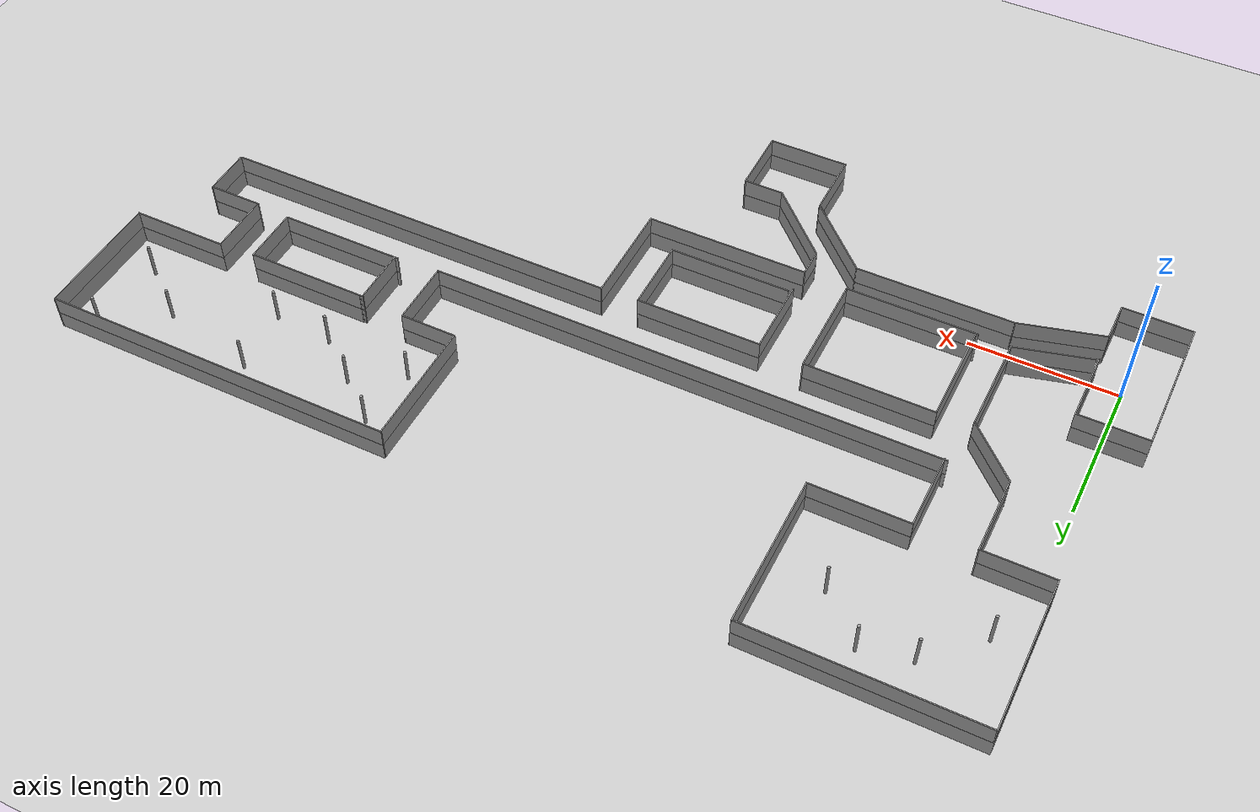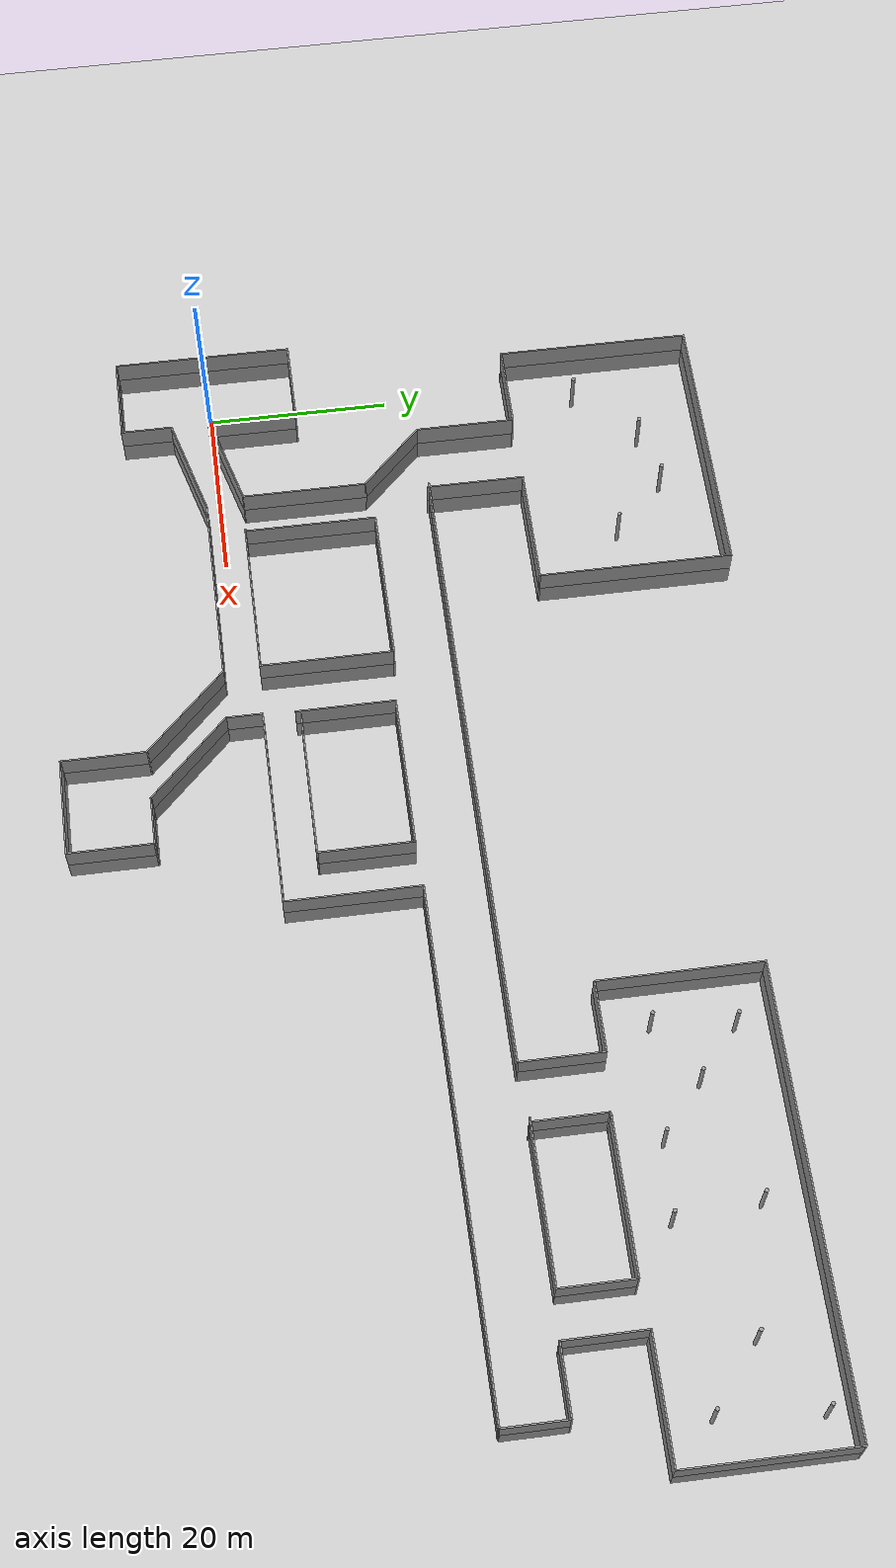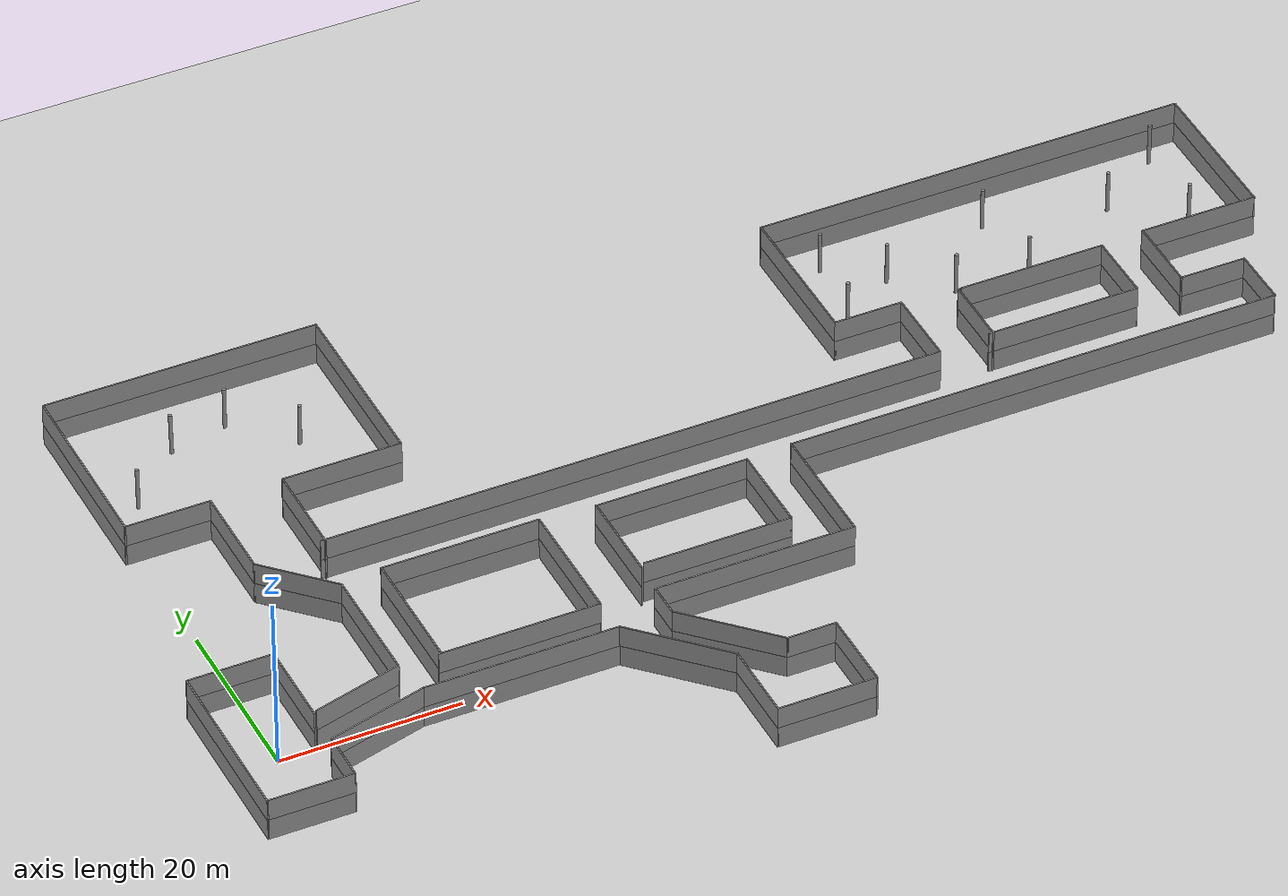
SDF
<sdf version="1.6">
 <world name="default">
  <light name="sun" type="directional">
   <pose>0 0 10 0 -0 0</pose>
   <diffuse>0.8 0.8 0.8 1</diffuse>
   <specular>0.2 0.2 0.2 1</specular>
   <attenuation>
    <range>1000</range>
    <constant>0.9</constant>
    <linear>0.01</linear>
    <quadratic>0.001</quadratic>
   </attenuation>
   <direction>-0.5 0.1 -0.9</direction>
  </light>
  <model name="ground_plane">
   <static>1</static>
   <link name="link">
    <collision name="collision">
     <geometry><plane><normal>0 0 1</normal><size>100 100</size></plane></geometry>
     <surface><friction><ode><mu>100</mu><mu2>50</mu2></ode></friction></surface>
    </collision>
    <visual name="visual">
     <cast_shadows>0</cast_shadows>
     <geometry><plane><normal>0 0 1</normal><size>100 100</size></plane></geometry>
     <material>
      <script><uri>file://media/materials/scripts/gazebo.material</uri><name>Gazebo/Grey</name></script>
     </material>
    </visual>
   </link>
  </model>
  <gravity>0 0 -9.8</gravity>
  <magnetic_field>6e-06 2.3e-05 -4.2e-05</magnetic_field>
  <atmosphere type="adiabatic"/>
  <physics name="default_physics" default="0" type="ode">
   <max_step_size>0.001</max_step_size>
   <real_time_factor>1</real_time_factor>
   <real_time_update_rate>1000</real_time_update_rate>
  </physics>
  <scene><ambient>0.4 0.4 0.4 1</ambient><background>0.7 0.7 0.7 1</background><shadows>1</shadows></scene>
  <audio><device>default</device></audio>
  <spherical_coordinates>
   <surface_model>EARTH_WGS84</surface_model>
   <latitude_deg>0</latitude_deg>
   <longitude_deg>0</longitude_deg>
   <elevation>0</elevation>
   <heading_deg>0</heading_deg>
  </spherical_coordinates>
  <model name="MultiExploreWorld">
   <pose>60 17.8179 0 0 -0 0</pose>
   <link name="Wall_10">
    <collision name="Wall_10_Collision">
     <geometry><box><size>9.5 0.15 2.5</size></box></geometry>
     <pose>0 0 1.25 0 -0 0</pose>
    </collision>
    <visual name="Wall_10_Visual">
     <pose>0 0 1.25 0 -0 0</pose>
     <geometry><box><size>9.5 0.15 2.5</size></box></geometry>
     <material>
      <script><uri>file://media/materials/scripts/gazebo.material</uri><name>Gazebo/Grey</name></script>
      <ambient>1 1 1 1</ambient>
     </material>
     <meta><layer>0</layer></meta>
    </visual>
    <pose>-60.789 -27.8261 0 0 -0 0</pose>
   </link>
   <link name="Wall_11">
    <collision name="Wall_11_Collision">
     <geometry><box><size>5.75 0.15 2.5</size></box></geometry>
     <pose>0 0 1.25 0 -0 0</pose>
    </collision>
    <visual name="Wall_11_Visual">
     <pose>0 0 1.25 0 -0 0</pose>
     <geometry><box><size>5.75 0.15 2.5</size></box></geometry>
     <material>
      <script><uri>file://media/materials/scripts/gazebo.material</uri><name>Gazebo/Grey</name></script>
      <ambient>1 1 1 1</ambient>
     </material>
     <meta><layer>0</layer></meta>
    </visual>
    <pose>-56.114 -25.0261 0 0 -0 1.5708</pose>
   </link>
   <link name="Wall_12">
    <collision name="Wall_12_Collision">
     <geometry><box><size>11.75 0.15 2.5</size></box></geometry>
     <pose>0 0 1.25 0 -0 0</pose>
    </collision>
    <visual name="Wall_12_Visual">
     <pose>0 0 1.25 0 -0 0</pose>
     <geometry><box><size>11.75 0.15 2.5</size></box></geometry>
     <material>
      <script><uri>file://media/materials/scripts/gazebo.material</uri><name>Gazebo/Grey</name></script>
      <ambient>1 1 1 1</ambient>
     </material>
     <meta><layer>0</layer></meta>
    </visual>
    <pose>-50.5116 -20.7249 0 0 -0 0.261799</pose>
   </link>
   <link name="Wall_13">
    <collision name="Wall_13_Collision">
     <geometry><box><size>21.5 0.15 2.5</size></box></geometry>
     <pose>0 0 1.25 0 -0 0</pose>
    </collision>
    <visual name="Wall_13_Visual">
     <pose>0 0 1.25 0 -0 0</pose>
     <geometry><box><size>21.5 0.15 2.5</size></box></geometry>
     <material>
      <script><uri>file://media/materials/scripts/gazebo.material</uri><name>Gazebo/Grey</name></script>
      <ambient>1 1 1 1</ambient>
     </material>
     <meta><layer>0</layer></meta>
    </visual>
    <pose>-34.2342 -19.2238 0 0 -0 0</pose>
   </link>
   <link name="Wall_14">
    <collision name="Wall_14_Collision">
     <geometry><box><size>12.5 0.15 2.5</size></box></geometry>
     <pose>0 0 1.25 0 -0 0</pose>
    </collision>
    <visual name="Wall_14_Visual">
     <pose>0 0 1.25 0 -0 0</pose>
     <geometry><box><size>12.5 0.15 2.5</size></box></geometry>
     <material>
      <script><uri>file://media/materials/scripts/gazebo.material</uri><name>Gazebo/Grey</name></script>
      <ambient>1 1 1 1</ambient>
     </material>
     <meta><layer>0</layer></meta>
    </visual>
    <pose>-19.1929 -23.5902 0 0 -0 -0.785398</pose>
   </link>
   <link name="Wall_15">
    <collision name="Wall_15_Collision">
     <geometry><box><size>9.25 0.15 2.5</size></box></geometry>
     <pose>0 0 1.25 0 -0 0</pose>
    </collision>
    <visual name="Wall_15_Visual">
     <pose>0 0 1.25 0 -0 0</pose>
     <geometry><box><size>9.25 0.15 2.5</size></box></geometry>
     <material>
      <script><uri>file://media/materials/scripts/gazebo.material</uri><name>Gazebo/Grey</name></script>
      <ambient>1 1 1 1</ambient>
     </material>
     <meta><layer>0</layer></meta>
    </visual>
    <pose>-14.8265 -32.5066 0 0 -0 -1.5708</pose>
   </link>
   <link name="Wall_16">
    <collision name="Wall_16_Collision">
     <geometry><box><size>11 0.15 2.5</size></box></geometry>
     <pose>0 0 1.25 0 -0 0</pose>
    </collision>
    <visual name="Wall_16_Visual">
     <pose>0 0 1.25 0 -0 0</pose>
     <geometry><box><size>11 0.15 2.5</size></box></geometry>
     <material>
      <script><uri>file://media/materials/scripts/gazebo.material</uri><name>Gazebo/Grey</name></script>
      <ambient>1 1 1 1</ambient>
     </material>
     <meta><layer>0</layer></meta>
    </visual>
    <pose>-9.40147 -37.0566 0 0 -0 0</pose>
   </link>
   <link name="Wall_17">
    <collision name="Wall_17_Collision">
     <geometry><box><size>9.25 0.15 2.5</size></box></geometry>
     <pose>0 0 1.25 0 -0 0</pose>
    </collision>
    <visual name="Wall_17_Visual">
     <pose>0 0 1.25 0 -0 0</pose>
     <geometry><box><size>9.25 0.15 2.5</size></box></geometry>
     <material>
      <script><uri>file://media/materials/scripts/gazebo.material</uri><name>Gazebo/Grey</name></script>
      <ambient>1 1 1 1</ambient>
     </material>
     <meta><layer>0</layer></meta>
    </visual>
    <pose>-3.97648 -32.5066 0 0 -0 1.5708</pose>
   </link>
   <link name="Wall_24">
    <collision name="Wall_24_Collision">
     <geometry><box><size>6.75 0.15 2.5</size></box></geometry>
     <pose>0 0 1.25 0 -0 0</pose>
    </collision>
    <visual name="Wall_24_Visual">
     <pose>0 0 1.25 0 -0 0</pose>
     <geometry><box><size>6.75 0.15 2.5</size></box></geometry>
     <material>
      <script><uri>file://media/materials/scripts/gazebo.material</uri><name>Gazebo/Grey</name></script>
      <ambient>1 1 1 1</ambient>
     </material>
     <meta><layer>0</layer></meta>
    </visual>
    <pose>59.714 2.20299 0 0 -0 1.5708</pose>
   </link>
   <link name="Wall_25">
    <collision name="Wall_25_Collision">
     <geometry><box><size>7.5 0.15 2.5</size></box></geometry>
     <pose>0 0 1.25 0 -0 0</pose>
    </collision>
    <visual name="Wall_25_Visual">
     <pose>0 0 1.25 0 -0 0</pose>
     <geometry><box><size>7.5 0.15 2.5</size></box></geometry>
     <material>
      <script><uri>file://media/materials/scripts/gazebo.material</uri><name>Gazebo/Grey</name></script>
      <ambient>1 1 1 1</ambient>
     </material>
     <meta><layer>0</layer></meta>
    </visual>
    <pose>56.039 5.50299 0 0 -0 3.14159</pose>
   </link>
   <link name="Wall_26">
    <collision name="Wall_26_Collision">
     <geometry><box><size>8.75 0.15 2.5</size></box></geometry>
     <pose>0 0 1.25 0 -0 0</pose>
    </collision>
    <visual name="Wall_26_Visual">
     <pose>0 0 1.25 0 -0 0</pose>
     <geometry><box><size>8.75 0.15 2.5</size></box></geometry>
     <material>
      <script><uri>file://media/materials/scripts/gazebo.material</uri><name>Gazebo/Grey</name></script>
      <ambient>1 1 1 1</ambient>
     </material>
     <meta><layer>0</layer></meta>
    </visual>
    <pose>52.364 9.80299 0 0 -0 1.5708</pose>
   </link>
   <link name="Wall_27">
    <collision name="Wall_27_Collision">
     <geometry><box><size>13.25 0.15 2.5</size></box></geometry>
     <pose>0 0 1.25 0 -0 0</pose>
    </collision>
    <visual name="Wall_27_Visual">
     <pose>0 0 1.25 0 -0 0</pose>
     <geometry><box><size>13.25 0.15 2.5</size></box></geometry>
     <material>
      <script><uri>file://media/materials/scripts/gazebo.material</uri><name>Gazebo/Grey</name></script>
      <ambient>1 1 1 1</ambient>
     </material>
     <meta><layer>0</layer></meta>
    </visual>
    <pose>58.914 14.103 0 0 -0 0</pose>
   </link>
   <link name="Wall_28">
    <collision name="Wall_28_Collision">
     <geometry><box><size>17.75 0.15 2.5</size></box></geometry>
     <pose>0 0 1.25 0 -0 0</pose>
    </collision>
    <visual name="Wall_28_Visual">
     <pose>0 0 1.25 0 -0 0</pose>
     <geometry><box><size>17.75 0.15 2.5</size></box></geometry>
     <material>
      <script><uri>file://media/materials/scripts/gazebo.material</uri><name>Gazebo/Grey</name></script>
      <ambient>1 1 1 1</ambient>
     </material>
     <meta><layer>0</layer></meta>
    </visual>
    <pose>65.464 22.903 0 0 -0 1.5708</pose>
   </link>
   <link name="Wall_29">
    <collision name="Wall_29_Collision">
     <geometry><box><size>48.75 0.15 2.5</size></box></geometry>
     <pose>0 0 1.25 0 -0 0</pose>
    </collision>
    <visual name="Wall_29_Visual">
     <pose>0 0 1.25 0 -0 0</pose>
     <geometry><box><size>48.75 0.15 2.5</size></box></geometry>
     <material>
      <script><uri>file://media/materials/scripts/gazebo.material</uri><name>Gazebo/Grey</name></script>
      <ambient>1 1 1 1</ambient>
     </material>
     <meta><layer>0</layer></meta>
    </visual>
    <pose>41.164 31.703 0 0 -0 3.14159</pose>
   </link>
   <link name="Wall_3">
    <collision name="Wall_3_Collision">
     <geometry><box><size>10 0.15 2.5</size></box></geometry>
     <pose>0 0 1.25 0 -0 0</pose>
    </collision>
    <visual name="Wall_3_Visual">
     <pose>0 0 1.25 0 -0 0</pose>
     <geometry><box><size>10 0.15 2.5</size></box></geometry>
     <material>
      <script><uri>file://media/materials/scripts/gazebo.material</uri><name>Gazebo/Grey</name></script>
      <ambient>1 1 1 1</ambient>
     </material>
     <meta><layer>0</layer></meta>
    </visual>
    <pose>-56.114 -13.1511 0 0 -0 1.5708</pose>
   </link>
   <link name="Wall_32">
    <collision name="Wall_32_Collision">
     <geometry><box><size>17.5 0.15 2.5</size></box></geometry>
     <pose>0 0 1.25 0 -0 0</pose>
    </collision>
    <visual name="Wall_32_Visual">
     <pose>0 0 1.25 0 -0 0</pose>
     <geometry><box><size>17.5 0.15 2.5</size></box></geometry>
     <material>
      <script><uri>file://media/materials/scripts/gazebo.material</uri><name>Gazebo/Grey</name></script>
      <ambient>1 1 1 1</ambient>
     </material>
     <meta><layer>0</layer></meta>
    </visual>
    <pose>16.864 23.028 0 0 -0 -1.5708</pose>
   </link>
   <link name="Wall_33">
    <collision name="Wall_33_Collision">
     <geometry><box><size>7.75 0.15 2.5</size></box></geometry>
     <pose>0 0 1.25 0 -0 0</pose>
    </collision>
    <visual name="Wall_33_Visual">
     <pose>0 0 1.25 0 -0 0</pose>
     <geometry><box><size>7.75 0.15 2.5</size></box></geometry>
     <material>
      <script><uri>file://media/materials/scripts/gazebo.material</uri><name>Gazebo/Grey</name></script>
      <ambient>1 1 1 1</ambient>
     </material>
     <meta><layer>0</layer></meta>
    </visual>
    <pose>20.664 14.353 0 0 -0 0</pose>
   </link>
   <link name="Wall_34">
    <collision name="Wall_34_Collision">
     <geometry><box><size>9 0.15 2.5</size></box></geometry>
     <pose>0 0 1.25 0 -0 0</pose>
    </collision>
    <visual name="Wall_34_Visual">
     <pose>0 0 1.25 0 -0 0</pose>
     <geometry><box><size>9 0.15 2.5</size></box></geometry>
     <material>
      <script><uri>file://media/materials/scripts/gazebo.material</uri><name>Gazebo/Grey</name></script>
      <ambient>1 1 1 1</ambient>
     </material>
     <meta><layer>0</layer></meta>
    </visual>
    <pose>24.464 9.92799 0 0 -0 -1.5708</pose>
   </link>
   <link name="Wall_35">
    <collision name="Wall_35_Collision">
     <geometry><box><size>69.5 0.15 2.5</size></box></geometry>
     <pose>0 0 1.25 0 -0 0</pose>
    </collision>
    <visual name="Wall_35_Visual">
     <pose>0 0 1.25 0 -0 0</pose>
     <geometry><box><size>69.5 0.15 2.5</size></box></geometry>
     <material>
      <script><uri>file://media/materials/scripts/gazebo.material</uri><name>Gazebo/Grey</name></script>
      <ambient>1 1 1 1</ambient>
     </material>
     <meta><layer>0</layer></meta>
    </visual>
    <pose>-10.211 5.50299 0 0 -0 3.14159</pose>
   </link>
   <link name="Wall_37">
    <collision name="Wall_37_Collision">
     <geometry><box><size>17.25 0.15 2.5</size></box></geometry>
     <pose>0 0 1.25 0 -0 0</pose>
    </collision>
    <visual name="Wall_37_Visual">
     <pose>0 0 1.25 0 -0 0</pose>
     <geometry><box><size>17.25 0.15 2.5</size></box></geometry>
     <material>
      <script><uri>file://media/materials/scripts/gazebo.material</uri><name>Gazebo/Grey</name></script>
      <ambient>1 1 1 1</ambient>
     </material>
     <meta><layer>0</layer></meta>
    </visual>
    <pose>38.8802 5.91246 0 0 -0 0</pose>
   </link>
   <link name="Wall_38">
    <collision name="Wall_38_Collision">
     <geometry><box><size>8 0.15 2.5</size></box></geometry>
     <pose>0 0 1.25 0 -0 0</pose>
    </collision>
    <visual name="Wall_38_Visual">
     <pose>0 0 1.25 0 -0 0</pose>
     <geometry><box><size>8 0.15 2.5</size></box></geometry>
     <material>
      <script><uri>file://media/materials/scripts/gazebo.material</uri><name>Gazebo/Grey</name></script>
      <ambient>1 1 1 1</ambient>
     </material>
     <meta><layer>0</layer></meta>
    </visual>
    <pose>47.4302 9.83746 0 0 -0 1.5708</pose>
   </link>
   <link name="Wall_39">
    <collision name="Wall_39_Collision">
     <geometry><box><size>16.5 0.15 2.5</size></box></geometry>
     <pose>0 0 1.25 0 -0 0</pose>
    </collision>
    <visual name="Wall_39_Visual">
     <pose>0 0 1.25 0 -0 0</pose>
     <geometry><box><size>16.5 0.15 2.5</size></box></geometry>
     <material>
      <script><uri>file://media/materials/scripts/gazebo.material</uri><name>Gazebo/Grey</name></script>
      <ambient>1 1 1 1</ambient>
     </material>
     <meta><layer>0</layer></meta>
    </visual>
    <pose>39.2552 13.7625 0 0 -0 3.14159</pose>
   </link>
   <link name="Wall_4">
    <collision name="Wall_4_Collision">
     <geometry><box><size>9.5 0.15 2.5</size></box></geometry>
     <pose>0 0 1.25 0 -0 0</pose>
    </collision>
    <visual name="Wall_4_Visual">
     <pose>0 0 1.25 0 -0 0</pose>
     <geometry><box><size>9.5 0.15 2.5</size></box></geometry>
     <material>
      <script><uri>file://media/materials/scripts/gazebo.material</uri><name>Gazebo/Grey</name></script>
      <ambient>1 1 1 1</ambient>
     </material>
     <meta><layer>0</layer></meta>
    </visual>
    <pose>-60.789 -8.22608 0 0 -0 3.14159</pose>
   </link>
   <link name="Wall_40">
    <collision name="Wall_40_Collision">
     <geometry><box><size>0.5 0.15 2.5</size></box></geometry>
     <pose>0 0 1.25 0 -0 0</pose>
    </collision>
    <visual name="Wall_40_Visual">
     <pose>0 0 1.25 0 -0 0</pose>
     <geometry><box><size>0.5 0.15 2.5</size></box></geometry>
     <material>
      <script><uri>file://media/materials/scripts/gazebo.material</uri><name>Gazebo/Grey</name></script>
      <ambient>1 1 1 1</ambient>
     </material>
     <meta><layer>0</layer></meta>
    </visual>
    <pose>30.9112 13.7172 0 0 -0 -2.87979</pose>
   </link>
   <link name="Wall_41">
    <collision name="Wall_41_Collision">
     <geometry><box><size>8 0.15 2.5</size></box></geometry>
     <pose>0 0 1.25 0 -0 0</pose>
    </collision>
    <visual name="Wall_41_Visual">
     <pose>0 0 1.25 0 -0 0</pose>
     <geometry><box><size>8 0.15 2.5</size></box></geometry>
     <material>
      <script><uri>file://media/materials/scripts/gazebo.material</uri><name>Gazebo/Grey</name></script>
      <ambient>1 1 1 1</ambient>
     </material>
     <meta><layer>0</layer></meta>
    </visual>
    <pose>30.7421 9.74687 0 0 -0 -1.5708</pose>
   </link>
   <link name="Wall_43">
    <collision name="Wall_43_Collision">
     <geometry><box><size>10.5 0.15 2.5</size></box></geometry>
     <pose>0 0 1.25 0 -0 0</pose>
    </collision>
    <visual name="Wall_43_Visual">
     <pose>0 0 1.25 0 -0 0</pose>
     <geometry><box><size>10.5 0.15 2.5</size></box></geometry>
     <material>
      <script><uri>file://media/materials/scripts/gazebo.material</uri><name>Gazebo/Grey</name></script>
      <ambient>1 1 1 1</ambient>
     </material>
     <meta><layer>0</layer></meta>
    </visual>
    <pose>-50.7332 -16.4443 0 0 -0 0.261799</pose>
   </link>
   <link name="Wall_44">
    <collision name="Wall_44_Collision">
     <geometry><box><size>13.75 0.15 2.5</size></box></geometry>
     <pose>0 0 1.25 0 -0 0</pose>
    </collision>
    <visual name="Wall_44_Visual">
     <pose>0 0 1.25 0 -0 0</pose>
     <geometry><box><size>13.75 0.15 2.5</size></box></geometry>
     <material>
      <script><uri>file://media/materials/scripts/gazebo.material</uri><name>Gazebo/Grey</name></script>
      <ambient>1 1 1 1</ambient>
     </material>
     <meta><layer>0</layer></meta>
    </visual>
    <pose>-45.7345 -8.3049 0 0 -0 1.5708</pose>
   </link>
   <link name="Wall_45">
    <collision name="Wall_45_Collision">
     <geometry><box><size>9.5 0.15 2.5</size></box></geometry>
     <pose>0 0 1.25 0 -0 0</pose>
    </collision>
    <visual name="Wall_45_Visual">
     <pose>0 0 1.25 0 -0 0</pose>
     <geometry><box><size>9.5 0.15 2.5</size></box></geometry>
     <material>
      <script><uri>file://media/materials/scripts/gazebo.material</uri><name>Gazebo/Grey</name></script>
      <ambient>1 1 1 1</ambient>
     </material>
     <meta><layer>0</layer></meta>
    </visual>
    <pose>-49.0403 1.80083 0 0 -0 2.35619</pose>
   </link>
   <link name="Wall_46">
    <collision name="Wall_46_Collision">
     <geometry><box><size>11 0.15 2.5</size></box></geometry>
     <pose>0 0 1.25 0 -0 0</pose>
    </collision>
    <visual name="Wall_46_Visual">
     <pose>0 0 1.25 0 -0 0</pose>
     <geometry><box><size>11 0.15 2.5</size></box></geometry>
     <material>
      <script><uri>file://media/materials/scripts/gazebo.material</uri><name>Gazebo/Grey</name></script>
      <ambient>1 1 1 1</ambient>
     </material>
     <meta><layer>0</layer></meta>
    </visual>
    <pose>-52.346 10.5316 0 0 -0 1.5708</pose>
   </link>
   <link name="Wall_47">
    <collision name="Wall_47_Collision">
     <geometry><box><size>9.5 0.15 2.5</size></box></geometry>
     <pose>0 0 1.25 0 -0 0</pose>
    </collision>
    <visual name="Wall_47_Visual">
     <pose>0 0 1.25 0 -0 0</pose>
     <geometry><box><size>9.5 0.15 2.5</size></box></geometry>
     <material>
      <script><uri>file://media/materials/scripts/gazebo.material</uri><name>Gazebo/Grey</name></script>
      <ambient>1 1 1 1</ambient>
     </material>
     <meta><layer>0</layer></meta>
    </visual>
    <pose>-57.021 15.9566 0 0 -0 3.14159</pose>
   </link>
   <link name="Wall_48">
    <collision name="Wall_48_Collision">
     <geometry><box><size>21.25 0.15 2.5</size></box></geometry>
     <pose>0 0 1.25 0 -0 0</pose>
    </collision>
    <visual name="Wall_48_Visual">
     <pose>0 0 1.25 0 -0 0</pose>
     <geometry><box><size>21.25 0.15 2.5</size></box></geometry>
     <material>
      <script><uri>file://media/materials/scripts/gazebo.material</uri><name>Gazebo/Grey</name></script>
      <ambient>1 1 1 1</ambient>
     </material>
     <meta><layer>0</layer></meta>
    </visual>
    <pose>-61.696 26.5066 0 0 -0 1.5708</pose>
   </link>
   <link name="Wall_49">
    <collision name="Wall_49_Collision">
     <geometry><box><size>30.5 0.15 2.5</size></box></geometry>
     <pose>0 0 1.25 0 -0 0</pose>
    </collision>
    <visual name="Wall_49_Visual">
     <pose>0 0 1.25 0 -0 0</pose>
     <geometry><box><size>30.5 0.15 2.5</size></box></geometry>
     <material>
      <script><uri>file://media/materials/scripts/gazebo.material</uri><name>Gazebo/Grey</name></script>
      <ambient>1 1 1 1</ambient>
     </material>
     <meta><layer>0</layer></meta>
    </visual>
    <pose>-46.521 37.0566 0 0 -0 0</pose>
   </link>
   <link name="Wall_5">
    <collision name="Wall_5_Collision">
     <geometry><box><size>19.75 0.15 2.5</size></box></geometry>
     <pose>0 0 1.25 0 -0 0</pose>
    </collision>
    <visual name="Wall_5_Visual">
     <pose>0 0 1.25 0 -0 0</pose>
     <geometry><box><size>19.75 0.15 2.5</size></box></geometry>
     <material>
      <script><uri>file://media/materials/scripts/gazebo.material</uri><name>Gazebo/Grey</name></script>
      <ambient>1 1 1 1</ambient>
     </material>
     <meta><layer>0</layer></meta>
    </visual>
    <pose>-65.464 -18.0261 0 0 -0 -1.5708</pose>
   </link>
   <link name="Wall_50">
    <collision name="Wall_50_Collision">
     <geometry><box><size>21.25 0.15 2.5</size></box></geometry>
     <pose>0 0 1.25 0 -0 0</pose>
    </collision>
    <visual name="Wall_50_Visual">
     <pose>0 0 1.25 0 -0 0</pose>
     <geometry><box><size>21.25 0.15 2.5</size></box></geometry>
     <material>
      <script><uri>file://media/materials/scripts/gazebo.material</uri><name>Gazebo/Grey</name></script>
      <ambient>1 1 1 1</ambient>
     </material>
     <meta><layer>0</layer></meta>
    </visual>
    <pose>-31.346 26.5066 0 0 -0 -1.5708</pose>
   </link>
   <link name="Wall_51">
    <collision name="Wall_51_Collision">
     <geometry><box><size>13.25 0.15 2.5</size></box></geometry>
     <pose>0 0 1.25 0 -0 0</pose>
    </collision>
    <visual name="Wall_51_Visual">
     <pose>0 0 1.25 0 -0 0</pose>
     <geometry><box><size>13.25 0.15 2.5</size></box></geometry>
     <material>
      <script><uri>file://media/materials/scripts/gazebo.material</uri><name>Gazebo/Grey</name></script>
      <ambient>1 1 1 1</ambient>
     </material>
     <meta><layer>0</layer></meta>
    </visual>
    <pose>-37.896 15.9566 0 0 -0 3.14159</pose>
   </link>
   <link name="Wall_52">
    <collision name="Wall_52_Collision">
     <geometry><box><size>10.75 0.15 2.5</size></box></geometry>
     <pose>0 0 1.25 0 -0 0</pose>
    </collision>
    <visual name="Wall_52_Visual">
     <pose>0 0 1.25 0 -0 0</pose>
     <geometry><box><size>10.75 0.15 2.5</size></box></geometry>
     <material>
      <script><uri>file://media/materials/scripts/gazebo.material</uri><name>Gazebo/Grey</name></script>
      <ambient>1 1 1 1</ambient>
     </material>
     <meta><layer>0</layer></meta>
    </visual>
    <pose>-44.446 10.6566 0 0 -0 -1.5708</pose>
   </link>
   <link name="Wall_55">
    <collision name="Wall_55_Collision">
     <geometry><box><size>17.75 0.15 2.5</size></box></geometry>
     <pose>0 0 1.25 0 -0 0</pose>
    </collision>
    <visual name="Wall_55_Visual">
     <pose>0 0 1.25 0 -0 0</pose>
     <geometry><box><size>17.75 0.15 2.5</size></box></geometry>
     <material>
      <script><uri>file://media/materials/scripts/gazebo.material</uri><name>Gazebo/Grey</name></script>
      <ambient>1 1 1 1</ambient>
     </material>
     <meta><layer>0</layer></meta>
    </visual>
    <pose>-32.5879 -15.2602 0 0 -0 0</pose>
   </link>
   <link name="Wall_56">
    <collision name="Wall_56_Collision">
     <geometry><box><size>14.5 0.15 2.5</size></box></geometry>
     <pose>0 0 1.25 0 -0 0</pose>
    </collision>
    <visual name="Wall_56_Visual">
     <pose>0 0 1.25 0 -0 0</pose>
     <geometry><box><size>14.5 0.15 2.5</size></box></geometry>
     <material>
      <script><uri>file://media/materials/scripts/gazebo.material</uri><name>Gazebo/Grey</name></script>
      <ambient>1 1 1 1</ambient>
     </material>
     <meta><layer>0</layer></meta>
    </visual>
    <pose>-23.7879 -8.08517 0 0 -0 1.5708</pose>
   </link>
   <link name="Wall_57">
    <collision name="Wall_57_Collision">
     <geometry><box><size>17.5 0.15 2.5</size></box></geometry>
     <pose>0 0 1.25 0 -0 0</pose>
    </collision>
    <visual name="Wall_57_Visual">
     <pose>0 0 1.25 0 -0 0</pose>
     <geometry><box><size>17.5 0.15 2.5</size></box></geometry>
     <material>
      <script><uri>file://media/materials/scripts/gazebo.material</uri><name>Gazebo/Grey</name></script>
      <ambient>1 1 1 1</ambient>
     </material>
     <meta><layer>0</layer></meta>
    </visual>
    <pose>-32.4629 -0.910175 0 0 -0 3.14159</pose>
   </link>
   <link name="Wall_58">
    <collision name="Wall_58_Collision">
     <geometry><box><size>14.5 0.15 2.5</size></box></geometry>
     <pose>0 0 1.25 0 -0 0</pose>
    </collision>
    <visual name="Wall_58_Visual">
     <pose>0 0 1.25 0 -0 0</pose>
     <geometry><box><size>14.5 0.15 2.5</size></box></geometry>
     <material>
      <script><uri>file://media/materials/scripts/gazebo.material</uri><name>Gazebo/Grey</name></script>
      <ambient>1 1 1 1</ambient>
     </material>
     <meta><layer>0</layer></meta>
    </visual>
    <pose>-41.1379 -8.08517 0 0 -0 -1.5708</pose>
   </link>
   <link name="Wall_64">
    <collision name="Wall_64_Collision">
     <geometry><box><size>5.5 0.15 2.5</size></box></geometry>
     <pose>0 0 1.25 0 -0 0</pose>
    </collision>
    <visual name="Wall_64_Visual">
     <pose>0 0 1.25 0 -0 0</pose>
     <geometry><box><size>5.5 0.15 2.5</size></box></geometry>
     <material>
      <script><uri>file://media/materials/scripts/gazebo.material</uri><name>Gazebo/Grey</name></script>
      <ambient>1 1 1 1</ambient>
     </material>
     <meta><layer>0</layer></meta>
    </visual>
    <pose>-6.65147 -27.9566 0 0 -0 3.14159</pose>
   </link>
   <link name="Wall_65">
    <collision name="Wall_65_Collision">
     <geometry><box><size>12.25 0.15 2.5</size></box></geometry>
     <pose>0 0 1.25 0 -0 0</pose>
    </collision>
    <visual name="Wall_65_Visual">
     <pose>0 0 1.25 0 -0 0</pose>
     <geometry><box><size>12.25 0.15 2.5</size></box></geometry>
     <material>
      <script><uri>file://media/materials/scripts/gazebo.material</uri><name>Gazebo/Grey</name></script>
      <ambient>1 1 1 1</ambient>
     </material>
     <meta><layer>0</layer></meta>
    </visual>
    <pose>-13.6045 -23.6786 0 0 -0 2.35619</pose>
   </link>
   <link name="Wall_66">
    <collision name="Wall_66_Collision">
     <geometry><box><size>4 0.15 2.5</size></box></geometry>
     <pose>0 0 1.25 0 -0 0</pose>
    </collision>
    <visual name="Wall_66_Visual">
     <pose>0 0 1.25 0 -0 0</pose>
     <geometry><box><size>4 0.15 2.5</size></box></geometry>
     <material>
      <script><uri>file://media/materials/scripts/gazebo.material</uri><name>Gazebo/Grey</name></script>
      <ambient>1 1 1 1</ambient>
     </material>
     <meta><layer>0</layer></meta>
    </visual>
    <pose>-17.8825 -17.4756 0 0 -0 1.5708</pose>
   </link>
   <link name="Wall_67">
    <collision name="Wall_67_Collision">
     <geometry><box><size>22.25 0.15 2.5</size></box></geometry>
     <pose>0 0 1.25 0 -0 0</pose>
    </collision>
    <visual name="Wall_67_Visual">
     <pose>0 0 1.25 0 -0 0</pose>
     <geometry><box><size>22.25 0.15 2.5</size></box></geometry>
     <material>
      <script><uri>file://media/materials/scripts/gazebo.material</uri><name>Gazebo/Grey</name></script>
      <ambient>1 1 1 1</ambient>
     </material>
     <meta><layer>0</layer></meta>
    </visual>
    <pose>-6.83247 -15.5506 0 0 -0 0</pose>
   </link>
   <link name="Wall_68">
    <collision name="Wall_68_Collision">
     <geometry><box><size>14.5 0.15 2.5</size></box></geometry>
     <pose>0 0 1.25 0 -0 0</pose>
    </collision>
    <visual name="Wall_68_Visual">
     <pose>0 0 1.25 0 -0 0</pose>
     <geometry><box><size>14.5 0.15 2.5</size></box></geometry>
     <material>
      <script><uri>file://media/materials/scripts/gazebo.material</uri><name>Gazebo/Grey</name></script>
      <ambient>1 1 1 1</ambient>
     </material>
     <meta><layer>0</layer></meta>
    </visual>
    <pose>4.21753 -8.37556 0 0 -0 1.5708</pose>
   </link>
   <link name="Wall_69">
    <collision name="Wall_69_Collision">
     <geometry><box><size>55.5 0.15 2.5</size></box></geometry>
     <pose>0 0 1.25 0 -0 0</pose>
    </collision>
    <visual name="Wall_69_Visual">
     <pose>0 0 1.25 0 -0 0</pose>
     <geometry><box><size>55.5 0.15 2.5</size></box></geometry>
     <material>
      <script><uri>file://media/materials/scripts/gazebo.material</uri><name>Gazebo/Grey</name></script>
      <ambient>1 1 1 1</ambient>
     </material>
     <meta><layer>0</layer></meta>
    </visual>
    <pose>31.8925 -1.20056 0 0 -0 0</pose>
   </link>
   <link name="Wall_71">
    <collision name="Wall_71_Collision">
     <geometry><box><size>10.75 0.15 2.5</size></box></geometry>
     <pose>0 0 1.25 0 -0 0</pose>
    </collision>
    <visual name="Wall_71_Visual">
     <pose>0 0 1.25 0 -0 0</pose>
     <geometry><box><size>10.75 0.15 2.5</size></box></geometry>
     <material>
      <script><uri>file://media/materials/scripts/gazebo.material</uri><name>Gazebo/Grey</name></script>
      <ambient>1 1 1 1</ambient>
     </material>
     <meta><layer>0</layer></meta>
    </visual>
    <pose>-17.718 -6.74789 0 0 -0 1.5708</pose>
   </link>
   <link name="Wall_72">
    <collision name="Wall_72_Collision">
     <geometry><box><size>17 0.15 2.5</size></box></geometry>
     <pose>0 0 1.25 0 -0 0</pose>
    </collision>
    <visual name="Wall_72_Visual">
     <pose>0 0 1.25 0 -0 0</pose>
     <geometry><box><size>17 0.15 2.5</size></box></geometry>
     <material>
      <script><uri>file://media/materials/scripts/gazebo.material</uri><name>Gazebo/Grey</name></script>
      <ambient>1 1 1 1</ambient>
     </material>
     <meta><layer>0</layer></meta>
    </visual>
    <pose>-9.29296 -1.44789 0 0 -0 0</pose>
   </link>
   <link name="Wall_73">
    <collision name="Wall_73_Collision">
     <geometry><box><size>10.25 0.15 2.5</size></box></geometry>
     <pose>0 0 1.25 0 -0 0</pose>
    </collision>
    <visual name="Wall_73_Visual">
     <pose>0 0 1.25 0 -0 0</pose>
     <geometry><box><size>10.25 0.15 2.5</size></box></geometry>
     <material>
      <script><uri>file://media/materials/scripts/gazebo.material</uri><name>Gazebo/Grey</name></script>
      <ambient>1 1 1 1</ambient>
     </material>
     <meta><layer>0</layer></meta>
    </visual>
    <pose>-0.867964 -6.49789 0 0 -0 -1.5708</pose>
   </link>
   <link name="Wall_74">
    <collision name="Wall_74_Collision">
     <geometry><box><size>16.5 0.15 2.5</size></box></geometry>
     <pose>0 0 1.25 0 -0 0</pose>
    </collision>
    <visual name="Wall_74_Visual">
     <pose>0 0 1.25 0 -0 0</pose>
     <geometry><box><size>16.5 0.15 2.5</size></box></geometry>
     <material>
      <script><uri>file://media/materials/scripts/gazebo.material</uri><name>Gazebo/Grey</name></script>
      <ambient>1 1 1 1</ambient>
     </material>
     <meta><layer>0</layer></meta>
    </visual>
    <pose>-9.04296 -11.5479 0 0 -0 3.14159</pose>
   </link>
   <static>1</static>
  </model>
  <model name="MultiExploreWorld_0">
   <pose>60 17.8179 2.5 0 -0 0</pose>
   <link name="Wall_10">
    <collision name="Wall_10_Collision">
     <geometry><box><size>9.5 0.15 2.5</size></box></geometry>
     <pose>0 0 1.25 0 -0 0</pose>
    </collision>
    <visual name="Wall_10_Visual">
     <pose>0 0 1.25 0 -0 0</pose>
     <geometry><box><size>9.5 0.15 2.5</size></box></geometry>
     <material>
      <script><uri>file://media/materials/scripts/gazebo.material</uri><name>Gazebo/Grey</name></script>
      <ambient>1 1 1 1</ambient>
     </material>
     <meta><layer>0</layer></meta>
    </visual>
    <pose>-60.789 -27.8261 0 0 -0 0</pose>
   </link>
   <link name="Wall_11">
    <collision name="Wall_11_Collision">
     <geometry><box><size>5.75 0.15 2.5</size></box></geometry>
     <pose>0 0 1.25 0 -0 0</pose>
    </collision>
    <visual name="Wall_11_Visual">
     <pose>0 0 1.25 0 -0 0</pose>
     <geometry><box><size>5.75 0.15 2.5</size></box></geometry>
     <material>
      <script><uri>file://media/materials/scripts/gazebo.material</uri><name>Gazebo/Grey</name></script>
      <ambient>1 1 1 1</ambient>
     </material>
     <meta><layer>0</layer></meta>
    </visual>
    <pose>-56.114 -25.0261 0 0 -0 1.5708</pose>
   </link>
   <link name="Wall_12">
    <collision name="Wall_12_Collision">
     <geometry><box><size>11.75 0.15 2.5</size></box></geometry>
     <pose>0 0 1.25 0 -0 0</pose>
    </collision>
    <visual name="Wall_12_Visual">
     <pose>0 0 1.25 0 -0 0</pose>
     <geometry><box><size>11.75 0.15 2.5</size></box></geometry>
     <material>
      <script><uri>file://media/materials/scripts/gazebo.material</uri><name>Gazebo/Grey</name></script>
      <ambient>1 1 1 1</ambient>
     </material>
     <meta><layer>0</layer></meta>
    </visual>
    <pose>-50.5116 -20.7249 0 0 -0 0.261799</pose>
   </link>
   <link name="Wall_13">
    <collision name="Wall_13_Collision">
     <geometry><box><size>21.5 0.15 2.5</size></box></geometry>
     <pose>0 0 1.25 0 -0 0</pose>
    </collision>
    <visual name="Wall_13_Visual">
     <pose>0 0 1.25 0 -0 0</pose>
     <geometry><box><size>21.5 0.15 2.5</size></box></geometry>
     <material>
      <script><uri>file://media/materials/scripts/gazebo.material</uri><name>Gazebo/Grey</name></script>
      <ambient>1 1 1 1</ambient>
     </material>
     <meta><layer>0</layer></meta>
    </visual>
    <pose>-34.2342 -19.2238 0 0 -0 0</pose>
   </link>
   <link name="Wall_14">
    <collision name="Wall_14_Collision">
     <geometry><box><size>12.5 0.15 2.5</size></box></geometry>
     <pose>0 0 1.25 0 -0 0</pose>
    </collision>
    <visual name="Wall_14_Visual">
     <pose>0 0 1.25 0 -0 0</pose>
     <geometry><box><size>12.5 0.15 2.5</size></box></geometry>
     <material>
      <script><uri>file://media/materials/scripts/gazebo.material</uri><name>Gazebo/Grey</name></script>
      <ambient>1 1 1 1</ambient>
     </material>
     <meta><layer>0</layer></meta>
    </visual>
    <pose>-19.1929 -23.5902 0 0 -0 -0.785398</pose>
   </link>
   <link name="Wall_15">
    <collision name="Wall_15_Collision">
     <geometry><box><size>9.25 0.15 2.5</size></box></geometry>
     <pose>0 0 1.25 0 -0 0</pose>
    </collision>
    <visual name="Wall_15_Visual">
     <pose>0 0 1.25 0 -0 0</pose>
     <geometry><box><size>9.25 0.15 2.5</size></box></geometry>
     <material>
      <script><uri>file://media/materials/scripts/gazebo.material</uri><name>Gazebo/Grey</name></script>
      <ambient>1 1 1 1</ambient>
     </material>
     <meta><layer>0</layer></meta>
    </visual>
    <pose>-14.8265 -32.5066 0 0 -0 -1.5708</pose>
   </link>
   <link name="Wall_16">
    <collision name="Wall_16_Collision">
     <geometry><box><size>11 0.15 2.5</size></box></geometry>
     <pose>0 0 1.25 0 -0 0</pose>
    </collision>
    <visual name="Wall_16_Visual">
     <pose>0 0 1.25 0 -0 0</pose>
     <geometry><box><size>11 0.15 2.5</size></box></geometry>
     <material>
      <script><uri>file://media/materials/scripts/gazebo.material</uri><name>Gazebo/Grey</name></script>
      <ambient>1 1 1 1</ambient>
     </material>
     <meta><layer>0</layer></meta>
    </visual>
    <pose>-9.40147 -37.0566 0 0 -0 0</pose>
   </link>
   <link name="Wall_17">
    <collision name="Wall_17_Collision">
     <geometry><box><size>9.25 0.15 2.5</size></box></geometry>
     <pose>0 0 1.25 0 -0 0</pose>
    </collision>
    <visual name="Wall_17_Visual">
     <pose>0 0 1.25 0 -0 0</pose>
     <geometry><box><size>9.25 0.15 2.5</size></box></geometry>
     <material>
      <script><uri>file://media/materials/scripts/gazebo.material</uri><name>Gazebo/Grey</name></script>
      <ambient>1 1 1 1</ambient>
     </material>
     <meta><layer>0</layer></meta>
    </visual>
    <pose>-3.97648 -32.5066 0 0 -0 1.5708</pose>
   </link>
   <link name="Wall_24">
    <collision name="Wall_24_Collision">
     <geometry><box><size>6.75 0.15 2.5</size></box></geometry>
     <pose>0 0 1.25 0 -0 0</pose>
    </collision>
    <visual name="Wall_24_Visual">
     <pose>0 0 1.25 0 -0 0</pose>
     <geometry><box><size>6.75 0.15 2.5</size></box></geometry>
     <material>
      <script><uri>file://media/materials/scripts/gazebo.material</uri><name>Gazebo/Grey</name></script>
      <ambient>1 1 1 1</ambient>
     </material>
     <meta><layer>0</layer></meta>
    </visual>
    <pose>59.714 2.20299 0 0 -0 1.5708</pose>
   </link>
   <link name="Wall_25">
    <collision name="Wall_25_Collision">
     <geometry><box><size>7.5 0.15 2.5</size></box></geometry>
     <pose>0 0 1.25 0 -0 0</pose>
    </collision>
    <visual name="Wall_25_Visual">
     <pose>0 0 1.25 0 -0 0</pose>
     <geometry><box><size>7.5 0.15 2.5</size></box></geometry>
     <material>
      <script><uri>file://media/materials/scripts/gazebo.material</uri><name>Gazebo/Grey</name></script>
      <ambient>1 1 1 1</ambient>
     </material>
     <meta><layer>0</layer></meta>
    </visual>
    <pose>56.039 5.50299 0 0 -0 3.14159</pose>
   </link>
   <link name="Wall_26">
    <collision name="Wall_26_Collision">
     <geometry><box><size>8.75 0.15 2.5</size></box></geometry>
     <pose>0 0 1.25 0 -0 0</pose>
    </collision>
    <visual name="Wall_26_Visual">
     <pose>0 0 1.25 0 -0 0</pose>
     <geometry><box><size>8.75 0.15 2.5</size></box></geometry>
     <material>
      <script><uri>file://media/materials/scripts/gazebo.material</uri><name>Gazebo/Grey</name></script>
      <ambient>1 1 1 1</ambient>
     </material>
     <meta><layer>0</layer></meta>
    </visual>
    <pose>52.364 9.80299 0 0 -0 1.5708</pose>
   </link>
   <link name="Wall_27">
    <collision name="Wall_27_Collision">
     <geometry><box><size>13.25 0.15 2.5</size></box></geometry>
     <pose>0 0 1.25 0 -0 0</pose>
    </collision>
    <visual name="Wall_27_Visual">
     <pose>0 0 1.25 0 -0 0</pose>
     <geometry><box><size>13.25 0.15 2.5</size></box></geometry>
     <material>
      <script><uri>file://media/materials/scripts/gazebo.material</uri><name>Gazebo/Grey</name></script>
      <ambient>1 1 1 1</ambient>
     </material>
     <meta><layer>0</layer></meta>
    </visual>
    <pose>58.914 14.103 0 0 -0 0</pose>
   </link>
   <link name="Wall_28">
    <collision name="Wall_28_Collision">
     <geometry><box><size>17.75 0.15 2.5</size></box></geometry>
     <pose>0 0 1.25 0 -0 0</pose>
    </collision>
    <visual name="Wall_28_Visual">
     <pose>0 0 1.25 0 -0 0</pose>
     <geometry><box><size>17.75 0.15 2.5</size></box></geometry>
     <material>
      <script><uri>file://media/materials/scripts/gazebo.material</uri><name>Gazebo/Grey</name></script>
      <ambient>1 1 1 1</ambient>
     </material>
     <meta><layer>0</layer></meta>
    </visual>
    <pose>65.464 22.903 0 0 -0 1.5708</pose>
   </link>
   <link name="Wall_29">
    <collision name="Wall_29_Collision">
     <geometry><box><size>48.75 0.15 2.5</size></box></geometry>
     <pose>0 0 1.25 0 -0 0</pose>
    </collision>
    <visual name="Wall_29_Visual">
     <pose>0 0 1.25 0 -0 0</pose>
     <geometry><box><size>48.75 0.15 2.5</size></box></geometry>
     <material>
      <script><uri>file://media/materials/scripts/gazebo.material</uri><name>Gazebo/Grey</name></script>
      <ambient>1 1 1 1</ambient>
     </material>
     <meta><layer>0</layer></meta>
    </visual>
    <pose>41.164 31.703 0 0 -0 3.14159</pose>
   </link>
   <link name="Wall_3">
    <collision name="Wall_3_Collision">
     <geometry><box><size>10 0.15 2.5</size></box></geometry>
     <pose>0 0 1.25 0 -0 0</pose>
    </collision>
    <visual name="Wall_3_Visual">
     <pose>0 0 1.25 0 -0 0</pose>
     <geometry><box><size>10 0.15 2.5</size></box></geometry>
     <material>
      <script><uri>file://media/materials/scripts/gazebo.material</uri><name>Gazebo/Grey</name></script>
      <ambient>1 1 1 1</ambient>
     </material>
     <meta><layer>0</layer></meta>
    </visual>
    <pose>-56.114 -13.1511 0 0 -0 1.5708</pose>
   </link>
   <link name="Wall_32">
    <collision name="Wall_32_Collision">
     <geometry><box><size>17.5 0.15 2.5</size></box></geometry>
     <pose>0 0 1.25 0 -0 0</pose>
    </collision>
    <visual name="Wall_32_Visual">
     <pose>0 0 1.25 0 -0 0</pose>
     <geometry><box><size>17.5 0.15 2.5</size></box></geometry>
     <material>
      <script><uri>file://media/materials/scripts/gazebo.material</uri><name>Gazebo/Grey</name></script>
      <ambient>1 1 1 1</ambient>
     </material>
     <meta><layer>0</layer></meta>
    </visual>
    <pose>16.864 23.028 0 0 -0 -1.5708</pose>
   </link>
   <link name="Wall_33">
    <collision name="Wall_33_Collision">
     <geometry><box><size>7.75 0.15 2.5</size></box></geometry>
     <pose>0 0 1.25 0 -0 0</pose>
    </collision>
    <visual name="Wall_33_Visual">
     <pose>0 0 1.25 0 -0 0</pose>
     <geometry><box><size>7.75 0.15 2.5</size></box></geometry>
     <material>
      <script><uri>file://media/materials/scripts/gazebo.material</uri><name>Gazebo/Grey</name></script>
      <ambient>1 1 1 1</ambient>
     </material>
     <meta><layer>0</layer></meta>
    </visual>
    <pose>20.664 14.353 0 0 -0 0</pose>
   </link>
   <link name="Wall_34">
    <collision name="Wall_34_Collision">
     <geometry><box><size>9 0.15 2.5</size></box></geometry>
     <pose>0 0 1.25 0 -0 0</pose>
    </collision>
    <visual name="Wall_34_Visual">
     <pose>0 0 1.25 0 -0 0</pose>
     <geometry><box><size>9 0.15 2.5</size></box></geometry>
     <material>
      <script><uri>file://media/materials/scripts/gazebo.material</uri><name>Gazebo/Grey</name></script>
      <ambient>1 1 1 1</ambient>
     </material>
     <meta><layer>0</layer></meta>
    </visual>
    <pose>24.464 9.92799 0 0 -0 -1.5708</pose>
   </link>
   <link name="Wall_35">
    <collision name="Wall_35_Collision">
     <geometry><box><size>69.5 0.15 2.5</size></box></geometry>
     <pose>0 0 1.25 0 -0 0</pose>
    </collision>
    <visual name="Wall_35_Visual">
     <pose>0 0 1.25 0 -0 0</pose>
     <geometry><box><size>69.5 0.15 2.5</size></box></geometry>
     <material>
      <script><uri>file://media/materials/scripts/gazebo.material</uri><name>Gazebo/Grey</name></script>
      <ambient>1 1 1 1</ambient>
     </material>
     <meta><layer>0</layer></meta>
    </visual>
    <pose>-10.211 5.50299 0 0 -0 3.14159</pose>
   </link>
   <link name="Wall_37">
    <collision name="Wall_37_Collision">
     <geometry><box><size>17.25 0.15 2.5</size></box></geometry>
     <pose>0 0 1.25 0 -0 0</pose>
    </collision>
    <visual name="Wall_37_Visual">
     <pose>0 0 1.25 0 -0 0</pose>
     <geometry><box><size>17.25 0.15 2.5</size></box></geometry>
     <material>
      <script><uri>file://media/materials/scripts/gazebo.material</uri><name>Gazebo/Grey</name></script>
      <ambient>1 1 1 1</ambient>
     </material>
     <meta><layer>0</layer></meta>
    </visual>
    <pose>38.8802 5.91246 0 0 -0 0</pose>
   </link>
   <link name="Wall_38">
    <collision name="Wall_38_Collision">
     <geometry><box><size>8 0.15 2.5</size></box></geometry>
     <pose>0 0 1.25 0 -0 0</pose>
    </collision>
    <visual name="Wall_38_Visual">
     <pose>0 0 1.25 0 -0 0</pose>
     <geometry><box><size>8 0.15 2.5</size></box></geometry>
     <material>
      <script><uri>file://media/materials/scripts/gazebo.material</uri><name>Gazebo/Grey</name></script>
      <ambient>1 1 1 1</ambient>
     </material>
     <meta><layer>0</layer></meta>
    </visual>
    <pose>47.4302 9.83746 0 0 -0 1.5708</pose>
   </link>
   <link name="Wall_39">
    <collision name="Wall_39_Collision">
     <geometry><box><size>16.5 0.15 2.5</size></box></geometry>
     <pose>0 0 1.25 0 -0 0</pose>
    </collision>
    <visual name="Wall_39_Visual">
     <pose>0 0 1.25 0 -0 0</pose>
     <geometry><box><size>16.5 0.15 2.5</size></box></geometry>
     <material>
      <script><uri>file://media/materials/scripts/gazebo.material</uri><name>Gazebo/Grey</name></script>
      <ambient>1 1 1 1</ambient>
     </material>
     <meta><layer>0</layer></meta>
    </visual>
    <pose>39.2552 13.7625 0 0 -0 3.14159</pose>
   </link>
   <link name="Wall_4">
    <collision name="Wall_4_Collision">
     <geometry><box><size>9.5 0.15 2.5</size></box></geometry>
     <pose>0 0 1.25 0 -0 0</pose>
    </collision>
    <visual name="Wall_4_Visual">
     <pose>0 0 1.25 0 -0 0</pose>
     <geometry><box><size>9.5 0.15 2.5</size></box></geometry>
     <material>
      <script><uri>file://media/materials/scripts/gazebo.material</uri><name>Gazebo/Grey</name></script>
      <ambient>1 1 1 1</ambient>
     </material>
     <meta><layer>0</layer></meta>
    </visual>
    <pose>-60.789 -8.22608 0 0 -0 3.14159</pose>
   </link>
   <link name="Wall_40">
    <collision name="Wall_40_Collision">
     <geometry><box><size>0.5 0.15 2.5</size></box></geometry>
     <pose>0 0 1.25 0 -0 0</pose>
    </collision>
    <visual name="Wall_40_Visual">
     <pose>0 0 1.25 0 -0 0</pose>
     <geometry><box><size>0.5 0.15 2.5</size></box></geometry>
     <material>
      <script><uri>file://media/materials/scripts/gazebo.material</uri><name>Gazebo/Grey</name></script>
      <ambient>1 1 1 1</ambient>
     </material>
     <meta><layer>0</layer></meta>
    </visual>
    <pose>30.9112 13.7172 0 0 -0 -2.87979</pose>
   </link>
   <link name="Wall_41">
    <collision name="Wall_41_Collision">
     <geometry><box><size>8 0.15 2.5</size></box></geometry>
     <pose>0 0 1.25 0 -0 0</pose>
    </collision>
    <visual name="Wall_41_Visual">
     <pose>0 0 1.25 0 -0 0</pose>
     <geometry><box><size>8 0.15 2.5</size></box></geometry>
     <material>
      <script><uri>file://media/materials/scripts/gazebo.material</uri><name>Gazebo/Grey</name></script>
      <ambient>1 1 1 1</ambient>
     </material>
     <meta><layer>0</layer></meta>
    </visual>
    <pose>30.7421 9.74687 0 0 -0 -1.5708</pose>
   </link>
   <link name="Wall_43">
    <collision name="Wall_43_Collision">
     <geometry><box><size>10.5 0.15 2.5</size></box></geometry>
     <pose>0 0 1.25 0 -0 0</pose>
    </collision>
    <visual name="Wall_43_Visual">
     <pose>0 0 1.25 0 -0 0</pose>
     <geometry><box><size>10.5 0.15 2.5</size></box></geometry>
     <material>
      <script><uri>file://media/materials/scripts/gazebo.material</uri><name>Gazebo/Grey</name></script>
      <ambient>1 1 1 1</ambient>
     </material>
     <meta><layer>0</layer></meta>
    </visual>
    <pose>-50.7332 -16.4443 0 0 -0 0.261799</pose>
   </link>
   <link name="Wall_44">
    <collision name="Wall_44_Collision">
     <geometry><box><size>13.75 0.15 2.5</size></box></geometry>
     <pose>0 0 1.25 0 -0 0</pose>
    </collision>
    <visual name="Wall_44_Visual">
     <pose>0 0 1.25 0 -0 0</pose>
     <geometry><box><size>13.75 0.15 2.5</size></box></geometry>
     <material>
      <script><uri>file://media/materials/scripts/gazebo.material</uri><name>Gazebo/Grey</name></script>
      <ambient>1 1 1 1</ambient>
     </material>
     <meta><layer>0</layer></meta>
    </visual>
    <pose>-45.7345 -8.3049 0 0 -0 1.5708</pose>
   </link>
   <link name="Wall_45">
    <collision name="Wall_45_Collision">
     <geometry><box><size>9.5 0.15 2.5</size></box></geometry>
     <pose>0 0 1.25 0 -0 0</pose>
    </collision>
    <visual name="Wall_45_Visual">
     <pose>0 0 1.25 0 -0 0</pose>
     <geometry><box><size>9.5 0.15 2.5</size></box></geometry>
     <material>
      <script><uri>file://media/materials/scripts/gazebo.material</uri><name>Gazebo/Grey</name></script>
      <ambient>1 1 1 1</ambient>
     </material>
     <meta><layer>0</layer></meta>
    </visual>
    <pose>-49.0403 1.80083 0 0 -0 2.35619</pose>
   </link>
   <link name="Wall_46">
    <collision name="Wall_46_Collision">
     <geometry><box><size>11 0.15 2.5</size></box></geometry>
     <pose>0 0 1.25 0 -0 0</pose>
    </collision>
    <visual name="Wall_46_Visual">
     <pose>0 0 1.25 0 -0 0</pose>
     <geometry><box><size>11 0.15 2.5</size></box></geometry>
     <material>
      <script><uri>file://media/materials/scripts/gazebo.material</uri><name>Gazebo/Grey</name></script>
      <ambient>1 1 1 1</ambient>
     </material>
     <meta><layer>0</layer></meta>
    </visual>
    <pose>-52.346 10.5316 0 0 -0 1.5708</pose>
   </link>
   <link name="Wall_47">
    <collision name="Wall_47_Collision">
     <geometry><box><size>9.5 0.15 2.5</size></box></geometry>
     <pose>0 0 1.25 0 -0 0</pose>
    </collision>
    <visual name="Wall_47_Visual">
     <pose>0 0 1.25 0 -0 0</pose>
     <geometry><box><size>9.5 0.15 2.5</size></box></geometry>
     <material>
      <script><uri>file://media/materials/scripts/gazebo.material</uri><name>Gazebo/Grey</name></script>
      <ambient>1 1 1 1</ambient>
     </material>
     <meta><layer>0</layer></meta>
    </visual>
    <pose>-57.021 15.9566 0 0 -0 3.14159</pose>
   </link>
   <link name="Wall_48">
    <collision name="Wall_48_Collision">
     <geometry><box><size>21.25 0.15 2.5</size></box></geometry>
     <pose>0 0 1.25 0 -0 0</pose>
    </collision>
    <visual name="Wall_48_Visual">
     <pose>0 0 1.25 0 -0 0</pose>
     <geometry><box><size>21.25 0.15 2.5</size></box></geometry>
     <material>
      <script><uri>file://media/materials/scripts/gazebo.material</uri><name>Gazebo/Grey</name></script>
      <ambient>1 1 1 1</ambient>
     </material>
     <meta><layer>0</layer></meta>
    </visual>
    <pose>-61.696 26.5066 0 0 -0 1.5708</pose>
   </link>
   <link name="Wall_49">
    <collision name="Wall_49_Collision">
     <geometry><box><size>30.5 0.15 2.5</size></box></geometry>
     <pose>0 0 1.25 0 -0 0</pose>
    </collision>
    <visual name="Wall_49_Visual">
     <pose>0 0 1.25 0 -0 0</pose>
     <geometry><box><size>30.5 0.15 2.5</size></box></geometry>
     <material>
      <script><uri>file://media/materials/scripts/gazebo.material</uri><name>Gazebo/Grey</name></script>
      <ambient>1 1 1 1</ambient>
     </material>
     <meta><layer>0</layer></meta>
    </visual>
    <pose>-46.521 37.0566 0 0 -0 0</pose>
   </link>
   <link name="Wall_5">
    <collision name="Wall_5_Collision">
     <geometry><box><size>19.75 0.15 2.5</size></box></geometry>
     <pose>0 0 1.25 0 -0 0</pose>
    </collision>
    <visual name="Wall_5_Visual">
     <pose>0 0 1.25 0 -0 0</pose>
     <geometry><box><size>19.75 0.15 2.5</size></box></geometry>
     <material>
      <script><uri>file://media/materials/scripts/gazebo.material</uri><name>Gazebo/Grey</name></script>
      <ambient>1 1 1 1</ambient>
     </material>
     <meta><layer>0</layer></meta>
    </visual>
    <pose>-65.464 -18.0261 0 0 -0 -1.5708</pose>
   </link>
   <link name="Wall_50">
    <collision name="Wall_50_Collision">
     <geometry><box><size>21.25 0.15 2.5</size></box></geometry>
     <pose>0 0 1.25 0 -0 0</pose>
    </collision>
    <visual name="Wall_50_Visual">
     <pose>0 0 1.25 0 -0 0</pose>
     <geometry><box><size>21.25 0.15 2.5</size></box></geometry>
     <material>
      <script><uri>file://media/materials/scripts/gazebo.material</uri><name>Gazebo/Grey</name></script>
      <ambient>1 1 1 1</ambient>
     </material>
     <meta><layer>0</layer></meta>
    </visual>
    <pose>-31.346 26.5066 0 0 -0 -1.5708</pose>
   </link>
   <link name="Wall_51">
    <collision name="Wall_51_Collision">
     <geometry><box><size>13.25 0.15 2.5</size></box></geometry>
     <pose>0 0 1.25 0 -0 0</pose>
    </collision>
    <visual name="Wall_51_Visual">
     <pose>0 0 1.25 0 -0 0</pose>
     <geometry><box><size>13.25 0.15 2.5</size></box></geometry>
     <material>
      <script><uri>file://media/materials/scripts/gazebo.material</uri><name>Gazebo/Grey</name></script>
      <ambient>1 1 1 1</ambient>
     </material>
     <meta><layer>0</layer></meta>
    </visual>
    <pose>-37.896 15.9566 0 0 -0 3.14159</pose>
   </link>
   <link name="Wall_52">
    <collision name="Wall_52_Collision">
     <geometry><box><size>10.75 0.15 2.5</size></box></geometry>
     <pose>0 0 1.25 0 -0 0</pose>
    </collision>
    <visual name="Wall_52_Visual">
     <pose>0 0 1.25 0 -0 0</pose>
     <geometry><box><size>10.75 0.15 2.5</size></box></geometry>
     <material>
      <script><uri>file://media/materials/scripts/gazebo.material</uri><name>Gazebo/Grey</name></script>
      <ambient>1 1 1 1</ambient>
     </material>
     <meta><layer>0</layer></meta>
    </visual>
    <pose>-44.446 10.6566 0 0 -0 -1.5708</pose>
   </link>
   <link name="Wall_55">
    <collision name="Wall_55_Collision">
     <geometry><box><size>17.75 0.15 2.5</size></box></geometry>
     <pose>0 0 1.25 0 -0 0</pose>
    </collision>
    <visual name="Wall_55_Visual">
     <pose>0 0 1.25 0 -0 0</pose>
     <geometry><box><size>17.75 0.15 2.5</size></box></geometry>
     <material>
      <script><uri>file://media/materials/scripts/gazebo.material</uri><name>Gazebo/Grey</name></script>
      <ambient>1 1 1 1</ambient>
     </material>
     <meta><layer>0</layer></meta>
    </visual>
    <pose>-32.5879 -15.2602 0 0 -0 0</pose>
   </link>
   <link name="Wall_56">
    <collision name="Wall_56_Collision">
     <geometry><box><size>14.5 0.15 2.5</size></box></geometry>
     <pose>0 0 1.25 0 -0 0</pose>
    </collision>
    <visual name="Wall_56_Visual">
     <pose>0 0 1.25 0 -0 0</pose>
     <geometry><box><size>14.5 0.15 2.5</size></box></geometry>
     <material>
      <script><uri>file://media/materials/scripts/gazebo.material</uri><name>Gazebo/Grey</name></script>
      <ambient>1 1 1 1</ambient>
     </material>
     <meta><layer>0</layer></meta>
    </visual>
    <pose>-23.7879 -8.08517 0 0 -0 1.5708</pose>
   </link>
   <link name="Wall_57">
    <collision name="Wall_57_Collision">
     <geometry><box><size>17.5 0.15 2.5</size></box></geometry>
     <pose>0 0 1.25 0 -0 0</pose>
    </collision>
    <visual name="Wall_57_Visual">
     <pose>0 0 1.25 0 -0 0</pose>
     <geometry><box><size>17.5 0.15 2.5</size></box></geometry>
     <material>
      <script><uri>file://media/materials/scripts/gazebo.material</uri><name>Gazebo/Grey</name></script>
      <ambient>1 1 1 1</ambient>
     </material>
     <meta><layer>0</layer></meta>
    </visual>
    <pose>-32.4629 -0.910175 0 0 -0 3.14159</pose>
   </link>
   <link name="Wall_58">
    <collision name="Wall_58_Collision">
     <geometry><box><size>14.5 0.15 2.5</size></box></geometry>
     <pose>0 0 1.25 0 -0 0</pose>
    </collision>
    <visual name="Wall_58_Visual">
     <pose>0 0 1.25 0 -0 0</pose>
     <geometry><box><size>14.5 0.15 2.5</size></box></geometry>
     <material>
      <script><uri>file://media/materials/scripts/gazebo.material</uri><name>Gazebo/Grey</name></script>
      <ambient>1 1 1 1</ambient>
     </material>
     <meta><layer>0</layer></meta>
    </visual>
    <pose>-41.1379 -8.08517 0 0 -0 -1.5708</pose>
   </link>
   <link name="Wall_64">
    <collision name="Wall_64_Collision">
     <geometry><box><size>5.5 0.15 2.5</size></box></geometry>
     <pose>0 0 1.25 0 -0 0</pose>
    </collision>
    <visual name="Wall_64_Visual">
     <pose>0 0 1.25 0 -0 0</pose>
     <geometry><box><size>5.5 0.15 2.5</size></box></geometry>
     <material>
      <script><uri>file://media/materials/scripts/gazebo.material</uri><name>Gazebo/Grey</name></script>
      <ambient>1 1 1 1</ambient>
     </material>
     <meta><layer>0</layer></meta>
    </visual>
    <pose>-6.65147 -27.9566 0 0 -0 3.14159</pose>
   </link>
   <link name="Wall_65">
    <collision name="Wall_65_Collision">
     <geometry><box><size>12.25 0.15 2.5</size></box></geometry>
     <pose>0 0 1.25 0 -0 0</pose>
    </collision>
    <visual name="Wall_65_Visual">
     <pose>0 0 1.25 0 -0 0</pose>
     <geometry><box><size>12.25 0.15 2.5</size></box></geometry>
     <material>
      <script><uri>file://media/materials/scripts/gazebo.material</uri><name>Gazebo/Grey</name></script>
      <ambient>1 1 1 1</ambient>
     </material>
     <meta><layer>0</layer></meta>
    </visual>
    <pose>-13.6045 -23.6786 0 0 -0 2.35619</pose>
   </link>
   <link name="Wall_66">
    <collision name="Wall_66_Collision">
     <geometry><box><size>4 0.15 2.5</size></box></geometry>
     <pose>0 0 1.25 0 -0 0</pose>
    </collision>
    <visual name="Wall_66_Visual">
     <pose>0 0 1.25 0 -0 0</pose>
     <geometry><box><size>4 0.15 2.5</size></box></geometry>
     <material>
      <script><uri>file://media/materials/scripts/gazebo.material</uri><name>Gazebo/Grey</name></script>
      <ambient>1 1 1 1</ambient>
     </material>
     <meta><layer>0</layer></meta>
    </visual>
    <pose>-17.8825 -17.4756 0 0 -0 1.5708</pose>
   </link>
   <link name="Wall_67">
    <collision name="Wall_67_Collision">
     <geometry><box><size>22.25 0.15 2.5</size></box></geometry>
     <pose>0 0 1.25 0 -0 0</pose>
    </collision>
    <visual name="Wall_67_Visual">
     <pose>0 0 1.25 0 -0 0</pose>
     <geometry><box><size>22.25 0.15 2.5</size></box></geometry>
     <material>
      <script><uri>file://media/materials/scripts/gazebo.material</uri><name>Gazebo/Grey</name></script>
      <ambient>1 1 1 1</ambient>
     </material>
     <meta><layer>0</layer></meta>
    </visual>
    <pose>-6.83247 -15.5506 0 0 -0 0</pose>
   </link>
   <link name="Wall_68">
    <collision name="Wall_68_Collision">
     <geometry><box><size>14.5 0.15 2.5</size></box></geometry>
     <pose>0 0 1.25 0 -0 0</pose>
    </collision>
    <visual name="Wall_68_Visual">
     <pose>0 0 1.25 0 -0 0</pose>
     <geometry><box><size>14.5 0.15 2.5</size></box></geometry>
     <material>
      <script><uri>file://media/materials/scripts/gazebo.material</uri><name>Gazebo/Grey</name></script>
      <ambient>1 1 1 1</ambient>
     </material>
     <meta><layer>0</layer></meta>
    </visual>
    <pose>4.21753 -8.37556 0 0 -0 1.5708</pose>
   </link>
   <link name="Wall_69">
    <collision name="Wall_69_Collision">
     <geometry><box><size>55.5 0.15 2.5</size></box></geometry>
     <pose>0 0 1.25 0 -0 0</pose>
    </collision>
    <visual name="Wall_69_Visual">
     <pose>0 0 1.25 0 -0 0</pose>
     <geometry><box><size>55.5 0.15 2.5</size></box></geometry>
     <material>
      <script><uri>file://media/materials/scripts/gazebo.material</uri><name>Gazebo/Grey</name></script>
      <ambient>1 1 1 1</ambient>
     </material>
     <meta><layer>0</layer></meta>
    </visual>
    <pose>31.8925 -1.20056 0 0 -0 0</pose>
   </link>
   <link name="Wall_71">
    <collision name="Wall_71_Collision">
     <geometry><box><size>10.75 0.15 2.5</size></box></geometry>
     <pose>0 0 1.25 0 -0 0</pose>
    </collision>
    <visual name="Wall_71_Visual">
     <pose>0 0 1.25 0 -0 0</pose>
     <geometry><box><size>10.75 0.15 2.5</size></box></geometry>
     <material>
      <script><uri>file://media/materials/scripts/gazebo.material</uri><name>Gazebo/Grey</name></script>
      <ambient>1 1 1 1</ambient>
     </material>
     <meta><layer>0</layer></meta>
    </visual>
    <pose>-17.718 -6.74789 0 0 -0 1.5708</pose>
   </link>
   <link name="Wall_72">
    <collision name="Wall_72_Collision">
     <geometry><box><size>17 0.15 2.5</size></box></geometry>
     <pose>0 0 1.25 0 -0 0</pose>
    </collision>
    <visual name="Wall_72_Visual">
     <pose>0 0 1.25 0 -0 0</pose>
     <geometry><box><size>17 0.15 2.5</size></box></geometry>
     <material>
      <script><uri>file://media/materials/scripts/gazebo.material</uri><name>Gazebo/Grey</name></script>
      <ambient>1 1 1 1</ambient>
     </material>
     <meta><layer>0</layer></meta>
    </visual>
    <pose>-9.29296 -1.44789 0 0 -0 0</pose>
   </link>
   <link name="Wall_73">
    <collision name="Wall_73_Collision">
     <geometry><box><size>10.25 0.15 2.5</size></box></geometry>
     <pose>0 0 1.25 0 -0 0</pose>
    </collision>
    <visual name="Wall_73_Visual">
     <pose>0 0 1.25 0 -0 0</pose>
     <geometry><box><size>10.25 0.15 2.5</size></box></geometry>
     <material>
      <script><uri>file://media/materials/scripts/gazebo.material</uri><name>Gazebo/Grey</name></script>
      <ambient>1 1 1 1</ambient>
     </material>
     <meta><layer>0</layer></meta>
    </visual>
    <pose>-0.867964 -6.49789 0 0 -0 -1.5708</pose>
   </link>
   <link name="Wall_74">
    <collision name="Wall_74_Collision">
     <geometry><box><size>16.5 0.15 2.5</size></box></geometry>
     <pose>0 0 1.25 0 -0 0</pose>
    </collision>
    <visual name="Wall_74_Visual">
     <pose>0 0 1.25 0 -0 0</pose>
     <geometry><box><size>16.5 0.15 2.5</size></box></geometry>
     <material>
      <script><uri>file://media/materials/scripts/gazebo.material</uri><name>Gazebo/Grey</name></script>
      <ambient>1 1 1 1</ambient>
     </material>
     <meta><layer>0</layer></meta>
    </visual>
    <pose>-9.04296 -11.5479 0 0 -0 3.14159</pose>
   </link>
   <static>1</static>
  </model>
  <model name="empty_pillar">
   <link name="link">
    <inertial>
     <mass>1</mass>
     <inertia><ixx>0.145833</ixx><ixy>0</ixy><ixz>0</ixz><iyy>0.145833</iyy><iyz>0</iyz><izz>0.125</izz></inertia>
    </inertial>
    <visual name="visual">
     <geometry><cylinder><radius>0.2</radius><length>5</length></cylinder></geometry>
     <material>
      <script><name>Gazebo/Grey</name><uri>file://media/materials/scripts/gazebo.material</uri></script>
      <shader type="vertex"><normal_map>__default__</normal_map></shader>
      <ambient>0.3 0.3 0.3 1</ambient>
      <diffuse>0.7 0.7 0.7 1</diffuse>
      <specular>0.01 0.01 0.01 1</specular>
      <emissive>0 0 0 1</emissive>
     </material>
    </visual>
    <collision name="collision">
     <geometry><cylinder><radius>0.05</radius><length>5</length></cylinder></geometry>
     <surface>
      <friction>
       <ode><mu>1</mu><mu2>1</mu2><fdir1>0 0 0</fdir1><slip1>0</slip1><slip2>0</slip2></ode>
       <torsional>
        <coefficient>1</coefficient>
        <patch_radius>0</patch_radius>
        <surface_radius>0</surface_radius>
        <use_patch_radius>1</use_patch_radius>
        <ode><slip>0</slip></ode>
       </torsional>
      </friction>
      <bounce><restitution_coefficient>0</restitution_coefficient><threshold>1e+06</threshold></bounce>
      <contact>
       <collide_without_contact>0</collide_without_contact>
       <collide_without_contact_bitmask>1</collide_without_contact_bitmask>
       <collide_bitmask>1</collide_bitmask>
       <ode>
        <soft_cfm>0</soft_cfm>
        <soft_erp>0.2</soft_erp>
        <kp>1e+13</kp>
        <kd>1</kd>
        <max_vel>0.01</max_vel>
        <min_depth>0</min_depth>
       </ode>
       <bullet>
        <split_impulse>1</split_impulse>
        <split_impulse_penetration_threshold>-0.01</split_impulse_penetration_threshold>
        <soft_cfm>0</soft_cfm>
        <soft_erp>0.2</soft_erp>
        <kp>1e+13</kp>
        <kd>1</kd>
       </bullet>
      </contact>
     </surface>
    </collision>
   </link>
   <static>0</static>
   <pose>81.9144 45.8591 2.5 -1e-06 -4e-06 0.000894</pose>
  </model>
  <model name="empty_pillar_0">
   <link name="link">
    <inertial>
     <mass>1</mass>
     <inertia><ixx>0.145833</ixx><ixy>0</ixy><ixz>0</ixz><iyy>0.145833</iyy><iyz>0</iyz><izz>0.125</izz></inertia>
    </inertial>
    <visual name="visual">
     <geometry><cylinder><radius>0.2</radius><length>5</length></cylinder></geometry>
     <material>
      <script><name>Gazebo/Grey</name><uri>file://media/materials/scripts/gazebo.material</uri></script>
      <shader type="vertex"><normal_map>__default__</normal_map></shader>
      <ambient>0.3 0.3 0.3 1</ambient>
      <diffuse>0.7 0.7 0.7 1</diffuse>
      <specular>0.01 0.01 0.01 1</specular>
      <emissive>0 0 0 1</emissive>
     </material>
    </visual>
    <collision name="collision">
     <geometry><cylinder><radius>0.05</radius><length>5</length></cylinder></geometry>
     <surface>
      <friction>
       <ode><mu>1</mu><mu2>1</mu2><fdir1>0 0 0</fdir1><slip1>0</slip1><slip2>0</slip2></ode>
       <torsional>
        <coefficient>1</coefficient>
        <patch_radius>0</patch_radius>
        <surface_radius>0</surface_radius>
        <use_patch_radius>1</use_patch_radius>
        <ode><slip>0</slip></ode>
       </torsional>
      </friction>
      <bounce><restitution_coefficient>0</restitution_coefficient><threshold>1e+06</threshold></bounce>
      <contact>
       <collide_without_contact>0</collide_without_contact>
       <collide_without_contact_bitmask>1</collide_without_contact_bitmask>
       <collide_bitmask>1</collide_bitmask>
       <ode>
        <soft_cfm>0</soft_cfm>
        <soft_erp>0.2</soft_erp>
        <kp>1e+13</kp>
        <kd>1</kd>
        <max_vel>0.01</max_vel>
        <min_depth>0</min_depth>
       </ode>
       <bullet>
        <split_impulse>1</split_impulse>
        <split_impulse_penetration_threshold>-0.01</split_impulse_penetration_threshold>
        <soft_cfm>0</soft_cfm>
        <soft_erp>0.2</soft_erp>
        <kp>1e+13</kp>
        <kd>1</kd>
       </bullet>
      </contact>
     </surface>
    </collision>
   </link>
   <static>0</static>
   <pose>87.4143 41.3092 2.5 1e-06 -3e-06 0.001559</pose>
  </model>
  <model name="empty_pillar_1">
   <link name="link">
    <inertial>
     <mass>1</mass>
     <inertia><ixx>0.145833</ixx><ixy>0</ixy><ixz>0</ixz><iyy>0.145833</iyy><iyz>0</iyz><izz>0.125</izz></inertia>
    </inertial>
    <visual name="visual">
     <geometry><cylinder><radius>0.2</radius><length>5</length></cylinder></geometry>
     <material>
      <script><name>Gazebo/Grey</name><uri>file://media/materials/scripts/gazebo.material</uri></script>
      <shader type="vertex"><normal_map>__default__</normal_map></shader>
      <ambient>0.3 0.3 0.3 1</ambient>
      <diffuse>0.7 0.7 0.7 1</diffuse>
      <specular>0.01 0.01 0.01 1</specular>
      <emissive>0 0 0 1</emissive>
     </material>
    </visual>
    <collision name="collision">
     <geometry><cylinder><radius>0.05</radius><length>5</length></cylinder></geometry>
     <surface>
      <friction>
       <ode><mu>1</mu><mu2>1</mu2><fdir1>0 0 0</fdir1><slip1>0</slip1><slip2>0</slip2></ode>
       <torsional>
        <coefficient>1</coefficient>
        <patch_radius>0</patch_radius>
        <surface_radius>0</surface_radius>
        <use_patch_radius>1</use_patch_radius>
        <ode><slip>0</slip></ode>
       </torsional>
      </friction>
      <bounce><restitution_coefficient>0</restitution_coefficient><threshold>1e+06</threshold></bounce>
      <contact>
       <collide_without_contact>0</collide_without_contact>
       <collide_without_contact_bitmask>1</collide_without_contact_bitmask>
       <collide_bitmask>1</collide_bitmask>
       <ode>
        <soft_cfm>0</soft_cfm>
        <soft_erp>0.2</soft_erp>
        <kp>1e+13</kp>
        <kd>1</kd>
        <max_vel>0.01</max_vel>
        <min_depth>0</min_depth>
       </ode>
       <bullet>
        <split_impulse>1</split_impulse>
        <split_impulse_penetration_threshold>-0.01</split_impulse_penetration_threshold>
        <soft_cfm>0</soft_cfm>
        <soft_erp>0.2</soft_erp>
        <kp>1e+13</kp>
        <kd>1</kd>
       </bullet>
      </contact>
     </surface>
    </collision>
   </link>
   <static>0</static>
   <pose>100.454 45.0911 2.49999 1e-06 -6e-06 0.000206</pose>
  </model>
  <model name="empty_pillar_2">
   <link name="link">
    <inertial>
     <mass>1</mass>
     <inertia><ixx>0.145833</ixx><ixy>0</ixy><ixz>0</ixz><iyy>0.145833</iyy><iyz>0</iyz><izz>0.125</izz></inertia>
    </inertial>
    <visual name="visual">
     <geometry><cylinder><radius>0.2</radius><length>5</length></cylinder></geometry>
     <material>
      <script><name>Gazebo/Grey</name><uri>file://media/materials/scripts/gazebo.material</uri></script>
      <shader type="vertex"><normal_map>__default__</normal_map></shader>
      <ambient>0.3 0.3 0.3 1</ambient>
      <diffuse>0.7 0.7 0.7 1</diffuse>
      <specular>0.01 0.01 0.01 1</specular>
      <emissive>0 0 0 1</emissive>
     </material>
    </visual>
    <collision name="collision">
     <geometry><cylinder><radius>0.05</radius><length>5</length></cylinder></geometry>
     <surface>
      <friction>
       <ode><mu>1</mu><mu2>1</mu2><fdir1>0 0 0</fdir1><slip1>0</slip1><slip2>0</slip2></ode>
       <torsional>
        <coefficient>1</coefficient>
        <patch_radius>0</patch_radius>
        <surface_radius>0</surface_radius>
        <use_patch_radius>1</use_patch_radius>
        <ode><slip>0</slip></ode>
       </torsional>
      </friction>
      <bounce><restitution_coefficient>0</restitution_coefficient><threshold>1e+06</threshold></bounce>
      <contact>
       <collide_without_contact>0</collide_without_contact>
       <collide_without_contact_bitmask>1</collide_without_contact_bitmask>
       <collide_bitmask>1</collide_bitmask>
       <ode>
        <soft_cfm>0</soft_cfm>
        <soft_erp>0.2</soft_erp>
        <kp>1e+13</kp>
        <kd>1</kd>
        <max_vel>0.01</max_vel>
        <min_depth>0</min_depth>
       </ode>
       <bullet>
        <split_impulse>1</split_impulse>
        <split_impulse_penetration_threshold>-0.01</split_impulse_penetration_threshold>
        <soft_cfm>0</soft_cfm>
        <soft_erp>0.2</soft_erp>
        <kp>1e+13</kp>
        <kd>1</kd>
       </bullet>
      </contact>
     </surface>
    </collision>
   </link>
   <static>0</static>
   <pose>113.651 42.0443 2.49999 -3e-06 1.5e-05 -0.000694</pose>
  </model>
  <model name="empty_pillar_3">
   <link name="link">
    <inertial>
     <mass>1</mass>
     <inertia><ixx>0.145833</ixx><ixy>0</ixy><ixz>0</ixz><iyy>0.145833</iyy><iyz>0</iyz><izz>0.125</izz></inertia>
    </inertial>
    <visual name="visual">
     <geometry><cylinder><radius>0.2</radius><length>5</length></cylinder></geometry>
     <material>
      <script><name>Gazebo/Grey</name><uri>file://media/materials/scripts/gazebo.material</uri></script>
      <shader type="vertex"><normal_map>__default__</normal_map></shader>
      <ambient>0.3 0.3 0.3 1</ambient>
      <diffuse>0.7 0.7 0.7 1</diffuse>
      <specular>0.01 0.01 0.01 1</specular>
      <emissive>0 0 0 1</emissive>
     </material>
    </visual>
    <collision name="collision">
     <geometry><cylinder><radius>0.05</radius><length>5</length></cylinder></geometry>
     <surface>
      <friction>
       <ode><mu>1</mu><mu2>1</mu2><fdir1>0 0 0</fdir1><slip1>0</slip1><slip2>0</slip2></ode>
       <torsional>
        <coefficient>1</coefficient>
        <patch_radius>0</patch_radius>
        <surface_radius>0</surface_radius>
        <use_patch_radius>1</use_patch_radius>
        <ode><slip>0</slip></ode>
       </torsional>
      </friction>
      <bounce><restitution_coefficient>0</restitution_coefficient><threshold>1e+06</threshold></bounce>
      <contact>
       <collide_without_contact>0</collide_without_contact>
       <collide_without_contact_bitmask>1</collide_without_contact_bitmask>
       <collide_bitmask>1</collide_bitmask>
       <ode>
        <soft_cfm>0</soft_cfm>
        <soft_erp>0.2</soft_erp>
        <kp>1e+13</kp>
        <kd>1</kd>
        <max_vel>0.01</max_vel>
        <min_depth>0</min_depth>
       </ode>
       <bullet>
        <split_impulse>1</split_impulse>
        <split_impulse_penetration_threshold>-0.01</split_impulse_penetration_threshold>
        <soft_cfm>0</soft_cfm>
        <soft_erp>0.2</soft_erp>
        <kp>1e+13</kp>
        <kd>1</kd>
       </bullet>
      </contact>
     </surface>
    </collision>
   </link>
   <static>0</static>
   <pose>101.335 36.0543 2.5 -2e-06 4e-06 -0.000478</pose>
  </model>
  <model name="empty_pillar_4">
   <link name="link">
    <inertial>
     <mass>1</mass>
     <inertia><ixx>0.145833</ixx><ixy>0</ixy><ixz>0</ixz><iyy>0.145833</iyy><iyz>0</iyz><izz>0.125</izz></inertia>
    </inertial>
    <visual name="visual">
     <geometry><cylinder><radius>0.2</radius><length>5</length></cylinder></geometry>
     <material>
      <script><name>Gazebo/Grey</name><uri>file://media/materials/scripts/gazebo.material</uri></script>
      <shader type="vertex"><normal_map>__default__</normal_map></shader>
      <ambient>0.3 0.3 0.3 1</ambient>
      <diffuse>0.7 0.7 0.7 1</diffuse>
      <specular>0.01 0.01 0.01 1</specular>
      <emissive>0 0 0 1</emissive>
     </material>
    </visual>
    <collision name="collision">
     <geometry><cylinder><radius>0.05</radius><length>5</length></cylinder></geometry>
     <surface>
      <friction>
       <ode><mu>1</mu><mu2>1</mu2><fdir1>0 0 0</fdir1><slip1>0</slip1><slip2>0</slip2></ode>
       <torsional>
        <coefficient>1</coefficient>
        <patch_radius>0</patch_radius>
        <surface_radius>0</surface_radius>
        <use_patch_radius>1</use_patch_radius>
        <ode><slip>0</slip></ode>
       </torsional>
      </friction>
      <bounce><restitution_coefficient>0</restitution_coefficient><threshold>1e+06</threshold></bounce>
      <contact>
       <collide_without_contact>0</collide_without_contact>
       <collide_without_contact_bitmask>1</collide_without_contact_bitmask>
       <collide_bitmask>1</collide_bitmask>
       <ode>
        <soft_cfm>0</soft_cfm>
        <soft_erp>0.2</soft_erp>
        <kp>1e+13</kp>
        <kd>1</kd>
        <max_vel>0.01</max_vel>
        <min_depth>0</min_depth>
       </ode>
       <bullet>
        <split_impulse>1</split_impulse>
        <split_impulse_penetration_threshold>-0.01</split_impulse_penetration_threshold>
        <soft_cfm>0</soft_cfm>
        <soft_erp>0.2</soft_erp>
        <kp>1e+13</kp>
        <kd>1</kd>
       </bullet>
      </contact>
     </surface>
    </collision>
   </link>
   <static>0</static>
   <pose>121.321 47.2973 2.5 0 2e-06 -0.000496</pose>
  </model>
  <model name="empty_pillar_5">
   <link name="link">
    <inertial>
     <mass>1</mass>
     <inertia><ixx>0.145833</ixx><ixy>0</ixy><ixz>0</ixz><iyy>0.145833</iyy><iyz>0</iyz><izz>0.125</izz></inertia>
    </inertial>
    <visual name="visual">
     <geometry><cylinder><radius>0.2</radius><length>5</length></cylinder></geometry>
     <material>
      <script><name>Gazebo/Grey</name><uri>file://media/materials/scripts/gazebo.material</uri></script>
      <shader type="vertex"><normal_map>__default__</normal_map></shader>
      <ambient>0.3 0.3 0.3 1</ambient>
      <diffuse>0.7 0.7 0.7 1</diffuse>
      <specular>0.01 0.01 0.01 1</specular>
      <emissive>0 0 0 1</emissive>
     </material>
    </visual>
    <collision name="collision">
     <geometry><cylinder><radius>0.05</radius><length>5</length></cylinder></geometry>
     <surface>
      <friction>
       <ode><mu>1</mu><mu2>1</mu2><fdir1>0 0 0</fdir1><slip1>0</slip1><slip2>0</slip2></ode>
       <torsional>
        <coefficient>1</coefficient>
        <patch_radius>0</patch_radius>
        <surface_radius>0</surface_radius>
        <use_patch_radius>1</use_patch_radius>
        <ode><slip>0</slip></ode>
       </torsional>
      </friction>
      <bounce><restitution_coefficient>0</restitution_coefficient><threshold>1e+06</threshold></bounce>
      <contact>
       <collide_without_contact>0</collide_without_contact>
       <collide_without_contact_bitmask>1</collide_without_contact_bitmask>
       <collide_bitmask>1</collide_bitmask>
       <ode>
        <soft_cfm>0</soft_cfm>
        <soft_erp>0.2</soft_erp>
        <kp>1e+13</kp>
        <kd>1</kd>
        <max_vel>0.01</max_vel>
        <min_depth>0</min_depth>
       </ode>
       <bullet>
        <split_impulse>1</split_impulse>
        <split_impulse_penetration_threshold>-0.01</split_impulse_penetration_threshold>
        <soft_cfm>0</soft_cfm>
        <soft_erp>0.2</soft_erp>
        <kp>1e+13</kp>
        <kd>1</kd>
       </bullet>
      </contact>
     </surface>
    </collision>
   </link>
   <static>0</static>
   <pose>120.441 36.6767 2.49999 -2e-06 -6e-06 8e-06</pose>
  </model>
  <model name="empty_pillar_6">
   <link name="link">
    <inertial>
     <mass>1</mass>
     <inertia><ixx>0.145833</ixx><ixy>0</ixy><ixz>0</ixz><iyy>0.145833</iyy><iyz>0</iyz><izz>0.125</izz></inertia>
    </inertial>
    <visual name="visual">
     <geometry><cylinder><radius>0.2</radius><length>5</length></cylinder></geometry>
     <material>
      <script><name>Gazebo/Grey</name><uri>file://media/materials/scripts/gazebo.material</uri></script>
      <shader type="vertex"><normal_map>__default__</normal_map></shader>
      <ambient>0.3 0.3 0.3 1</ambient>
      <diffuse>0.7 0.7 0.7 1</diffuse>
      <specular>0.01 0.01 0.01 1</specular>
      <emissive>0 0 0 1</emissive>
     </material>
    </visual>
    <collision name="collision">
     <geometry><cylinder><radius>0.05</radius><length>5</length></cylinder></geometry>
     <surface>
      <friction>
       <ode><mu>1</mu><mu2>1</mu2><fdir1>0 0 0</fdir1><slip1>0</slip1><slip2>0</slip2></ode>
       <torsional>
        <coefficient>1</coefficient>
        <patch_radius>0</patch_radius>
        <surface_radius>0</surface_radius>
        <use_patch_radius>1</use_patch_radius>
        <ode><slip>0</slip></ode>
       </torsional>
      </friction>
      <bounce><restitution_coefficient>0</restitution_coefficient><threshold>1e+06</threshold></bounce>
      <contact>
       <collide_without_contact>0</collide_without_contact>
       <collide_without_contact_bitmask>1</collide_without_contact_bitmask>
       <collide_bitmask>1</collide_bitmask>
       <ode>
        <soft_cfm>0</soft_cfm>
        <soft_erp>0.2</soft_erp>
        <kp>1e+13</kp>
        <kd>1</kd>
        <max_vel>0.01</max_vel>
        <min_depth>0</min_depth>
       </ode>
       <bullet>
        <split_impulse>1</split_impulse>
        <split_impulse_penetration_threshold>-0.01</split_impulse_penetration_threshold>
        <soft_cfm>0</soft_cfm>
        <soft_erp>0.2</soft_erp>
        <kp>1e+13</kp>
        <kd>1</kd>
       </bullet>
      </contact>
     </surface>
    </collision>
   </link>
   <static>0</static>
   <pose>93.1477 36.7015 2.49999 -1e-06 -6e-06 0.000635</pose>
  </model>
  <model name="empty_pillar_7">
   <link name="link">
    <inertial>
     <mass>1</mass>
     <inertia><ixx>0.145833</ixx><ixy>0</ixy><ixz>0</ixz><iyy>0.145833</iyy><iyz>0</iyz><izz>0.125</izz></inertia>
    </inertial>
    <visual name="visual">
     <geometry><cylinder><radius>0.2</radius><length>5</length></cylinder></geometry>
     <material>
      <script><name>Gazebo/Grey</name><uri>file://media/materials/scripts/gazebo.material</uri></script>
      <shader type="vertex"><normal_map>__default__</normal_map></shader>
      <ambient>0.3 0.3 0.3 1</ambient>
      <diffuse>0.7 0.7 0.7 1</diffuse>
      <specular>0.01 0.01 0.01 1</specular>
      <emissive>0 0 0 1</emissive>
     </material>
    </visual>
    <collision name="collision">
     <geometry><cylinder><radius>0.05</radius><length>5</length></cylinder></geometry>
     <surface>
      <friction>
       <ode><mu>1</mu><mu2>1</mu2><fdir1>0 0 0</fdir1><slip1>0</slip1><slip2>0</slip2></ode>
       <torsional>
        <coefficient>1</coefficient>
        <patch_radius>0</patch_radius>
        <surface_radius>0</surface_radius>
        <use_patch_radius>1</use_patch_radius>
        <ode><slip>0</slip></ode>
       </torsional>
      </friction>
      <bounce><restitution_coefficient>0</restitution_coefficient><threshold>1e+06</threshold></bounce>
      <contact>
       <collide_without_contact>0</collide_without_contact>
       <collide_without_contact_bitmask>1</collide_without_contact_bitmask>
       <collide_bitmask>1</collide_bitmask>
       <ode>
        <soft_cfm>0</soft_cfm>
        <soft_erp>0.2</soft_erp>
        <kp>1e+13</kp>
        <kd>1</kd>
        <max_vel>0.01</max_vel>
        <min_depth>0</min_depth>
       </ode>
       <bullet>
        <split_impulse>1</split_impulse>
        <split_impulse_penetration_threshold>-0.01</split_impulse_penetration_threshold>
        <soft_cfm>0</soft_cfm>
        <soft_erp>0.2</soft_erp>
        <kp>1e+13</kp>
        <kd>1</kd>
       </bullet>
      </contact>
     </surface>
    </collision>
   </link>
   <static>0</static>
   <pose>80.9338 37.3588 2.49999 -1e-06 1e-06 -0.000321</pose>
  </model>
  <model name="empty_pillar_8">
   <link name="link">
    <inertial>
     <mass>1</mass>
     <inertia><ixx>0.145833</ixx><ixy>0</ixy><ixz>0</ixz><iyy>0.145833</iyy><iyz>0</iyz><izz>0.125</izz></inertia>
    </inertial>
    <visual name="visual">
     <geometry><cylinder><radius>0.2</radius><length>5</length></cylinder></geometry>
     <material>
      <script><name>Gazebo/Grey</name><uri>file://media/materials/scripts/gazebo.material</uri></script>
      <shader type="vertex"><normal_map>__default__</normal_map></shader>
      <ambient>0.3 0.3 0.3 1</ambient>
      <diffuse>0.7 0.7 0.7 1</diffuse>
      <specular>0.01 0.01 0.01 1</specular>
      <emissive>0 0 0 1</emissive>
     </material>
    </visual>
    <collision name="collision">
     <geometry><cylinder><radius>0.05</radius><length>5</length></cylinder></geometry>
     <surface>
      <friction>
       <ode><mu>1</mu><mu2>1</mu2><fdir1>0 0 0</fdir1><slip1>0</slip1><slip2>0</slip2></ode>
       <torsional>
        <coefficient>1</coefficient>
        <patch_radius>0</patch_radius>
        <surface_radius>0</surface_radius>
        <use_patch_radius>1</use_patch_radius>
        <ode><slip>0</slip></ode>
       </torsional>
      </friction>
      <bounce><restitution_coefficient>0</restitution_coefficient><threshold>1e+06</threshold></bounce>
      <contact>
       <collide_without_contact>0</collide_without_contact>
       <collide_without_contact_bitmask>1</collide_without_contact_bitmask>
       <collide_bitmask>1</collide_bitmask>
       <ode>
        <soft_cfm>0</soft_cfm>
        <soft_erp>0.2</soft_erp>
        <kp>1e+13</kp>
        <kd>1</kd>
        <max_vel>0.01</max_vel>
        <min_depth>0</min_depth>
       </ode>
       <bullet>
        <split_impulse>1</split_impulse>
        <split_impulse_penetration_threshold>-0.01</split_impulse_penetration_threshold>
        <soft_cfm>0</soft_cfm>
        <soft_erp>0.2</soft_erp>
        <kp>1e+13</kp>
        <kd>1</kd>
       </bullet>
      </contact>
     </surface>
    </collision>
   </link>
   <static>0</static>
   <pose>2.88849 41.4112 2.50007 -5e-06 -0.001384 -3e-06</pose>
  </model>
  <model name="empty_pillar_9">
   <link name="link">
    <inertial>
     <mass>1</mass>
     <inertia><ixx>0.145833</ixx><ixy>0</ixy><ixz>0</ixz><iyy>0.145833</iyy><iyz>0</iyz><izz>0.125</izz></inertia>
    </inertial>
    <visual name="visual">
     <geometry><cylinder><radius>0.2</radius><length>5</length></cylinder></geometry>
     <material>
      <script><name>Gazebo/Grey</name><uri>file://media/materials/scripts/gazebo.material</uri></script>
      <shader type="vertex"><normal_map>__default__</normal_map></shader>
      <ambient>0.3 0.3 0.3 1</ambient>
      <diffuse>0.7 0.7 0.7 1</diffuse>
      <specular>0.01 0.01 0.01 1</specular>
      <emissive>0 0 0 1</emissive>
     </material>
    </visual>
    <collision name="collision">
     <geometry><cylinder><radius>0.05</radius><length>5</length></cylinder></geometry>
     <surface>
      <friction>
       <ode><mu>1</mu><mu2>1</mu2><fdir1>0 0 0</fdir1><slip1>0</slip1><slip2>0</slip2></ode>
       <torsional>
        <coefficient>1</coefficient>
        <patch_radius>0</patch_radius>
        <surface_radius>0</surface_radius>
        <use_patch_radius>1</use_patch_radius>
        <ode><slip>0</slip></ode>
       </torsional>
      </friction>
      <bounce><restitution_coefficient>0</restitution_coefficient><threshold>1e+06</threshold></bounce>
      <contact>
       <collide_without_contact>0</collide_without_contact>
       <collide_without_contact_bitmask>1</collide_without_contact_bitmask>
       <collide_bitmask>1</collide_bitmask>
       <ode>
        <soft_cfm>0</soft_cfm>
        <soft_erp>0.2</soft_erp>
        <kp>1e+13</kp>
        <kd>1</kd>
        <max_vel>0.01</max_vel>
        <min_depth>0</min_depth>
       </ode>
       <bullet>
        <split_impulse>1</split_impulse>
        <split_impulse_penetration_threshold>-0.01</split_impulse_penetration_threshold>
        <soft_cfm>0</soft_cfm>
        <soft_erp>0.2</soft_erp>
        <kp>1e+13</kp>
        <kd>1</kd>
       </bullet>
      </contact>
     </surface>
    </collision>
   </link>
   <static>0</static>
   <pose>15.9188 49.3543 2.50029 -1.9e-05 0.007097 -2e-06</pose>
  </model>
  <model name="empty_pillar_10">
   <link name="link">
    <inertial>
     <mass>1</mass>
     <inertia><ixx>0.145833</ixx><ixy>0</ixy><ixz>0</ixz><iyy>0.145833</iyy><iyz>0</iyz><izz>0.125</izz></inertia>
    </inertial>
    <visual name="visual">
     <geometry><cylinder><radius>0.2</radius><length>5</length></cylinder></geometry>
     <material>
      <script><name>Gazebo/Grey</name><uri>file://media/materials/scripts/gazebo.material</uri></script>
      <shader type="vertex"><normal_map>__default__</normal_map></shader>
      <ambient>0.3 0.3 0.3 1</ambient>
      <diffuse>0.7 0.7 0.7 1</diffuse>
      <specular>0.01 0.01 0.01 1</specular>
      <emissive>0 0 0 1</emissive>
     </material>
    </visual>
    <collision name="collision">
     <geometry><cylinder><radius>0.05</radius><length>5</length></cylinder></geometry>
     <surface>
      <friction>
       <ode><mu>1</mu><mu2>1</mu2><fdir1>0 0 0</fdir1><slip1>0</slip1><slip2>0</slip2></ode>
       <torsional>
        <coefficient>1</coefficient>
        <patch_radius>0</patch_radius>
        <surface_radius>0</surface_radius>
        <use_patch_radius>1</use_patch_radius>
        <ode><slip>0</slip></ode>
       </torsional>
      </friction>
      <bounce><restitution_coefficient>0</restitution_coefficient><threshold>1e+06</threshold></bounce>
      <contact>
       <collide_without_contact>0</collide_without_contact>
       <collide_without_contact_bitmask>1</collide_without_contact_bitmask>
       <collide_bitmask>1</collide_bitmask>
       <ode>
        <soft_cfm>0</soft_cfm>
        <soft_erp>0.2</soft_erp>
        <kp>1e+13</kp>
        <kd>1</kd>
        <max_vel>0.01</max_vel>
        <min_depth>0</min_depth>
       </ode>
       <bullet>
        <split_impulse>1</split_impulse>
        <split_impulse_penetration_threshold>-0.01</split_impulse_penetration_threshold>
        <soft_cfm>0</soft_cfm>
        <soft_erp>0.2</soft_erp>
        <kp>1e+13</kp>
        <kd>1</kd>
       </bullet>
      </contact>
     </surface>
    </collision>
   </link>
   <static>0</static>
   <pose>21.7831 43.6464 2.50036 -2.9e-05 0.009874 -3e-06</pose>
  </model>
  <model name="empty_pillar_11">
   <link name="link">
    <inertial>
     <mass>1</mass>
     <inertia><ixx>0.145833</ixx><ixy>0</ixy><ixz>0</ixz><iyy>0.145833</iyy><iyz>0</iyz><izz>0.125</izz></inertia>
    </inertial>
    <visual name="visual">
     <geometry><cylinder><radius>0.2</radius><length>5</length></cylinder></geometry>
     <material>
      <script><name>Gazebo/Grey</name><uri>file://media/materials/scripts/gazebo.material</uri></script>
      <shader type="vertex"><normal_map>__default__</normal_map></shader>
      <ambient>0.3 0.3 0.3 1</ambient>
      <diffuse>0.7 0.7 0.7 1</diffuse>
      <specular>0.01 0.01 0.01 1</specular>
      <emissive>0 0 0 1</emissive>
     </material>
    </visual>
    <collision name="collision">
     <geometry><cylinder><radius>0.05</radius><length>5</length></cylinder></geometry>
     <surface>
      <friction>
       <ode><mu>1</mu><mu2>1</mu2><fdir1>0 0 0</fdir1><slip1>0</slip1><slip2>0</slip2></ode>
       <torsional>
        <coefficient>1</coefficient>
        <patch_radius>0</patch_radius>
        <surface_radius>0</surface_radius>
        <use_patch_radius>1</use_patch_radius>
        <ode><slip>0</slip></ode>
       </torsional>
      </friction>
      <bounce><restitution_coefficient>0</restitution_coefficient><threshold>1e+06</threshold></bounce>
      <contact>
       <collide_without_contact>0</collide_without_contact>
       <collide_without_contact_bitmask>1</collide_without_contact_bitmask>
       <collide_bitmask>1</collide_bitmask>
       <ode>
        <soft_cfm>0</soft_cfm>
        <soft_erp>0.2</soft_erp>
        <kp>1e+13</kp>
        <kd>1</kd>
        <max_vel>0.01</max_vel>
        <min_depth>0</min_depth>
       </ode>
       <bullet>
        <split_impulse>1</split_impulse>
        <split_impulse_penetration_threshold>-0.01</split_impulse_penetration_threshold>
        <soft_cfm>0</soft_cfm>
        <soft_erp>0.2</soft_erp>
        <kp>1e+13</kp>
        <kd>1</kd>
       </bullet>
      </contact>
     </surface>
    </collision>
   </link>
   <static>0</static>
   <pose>9.35329 47.9112 2.50037 -9.8e-05 -0.009842 -2e-06</pose>
  </model>
 </world>
</sdf>
